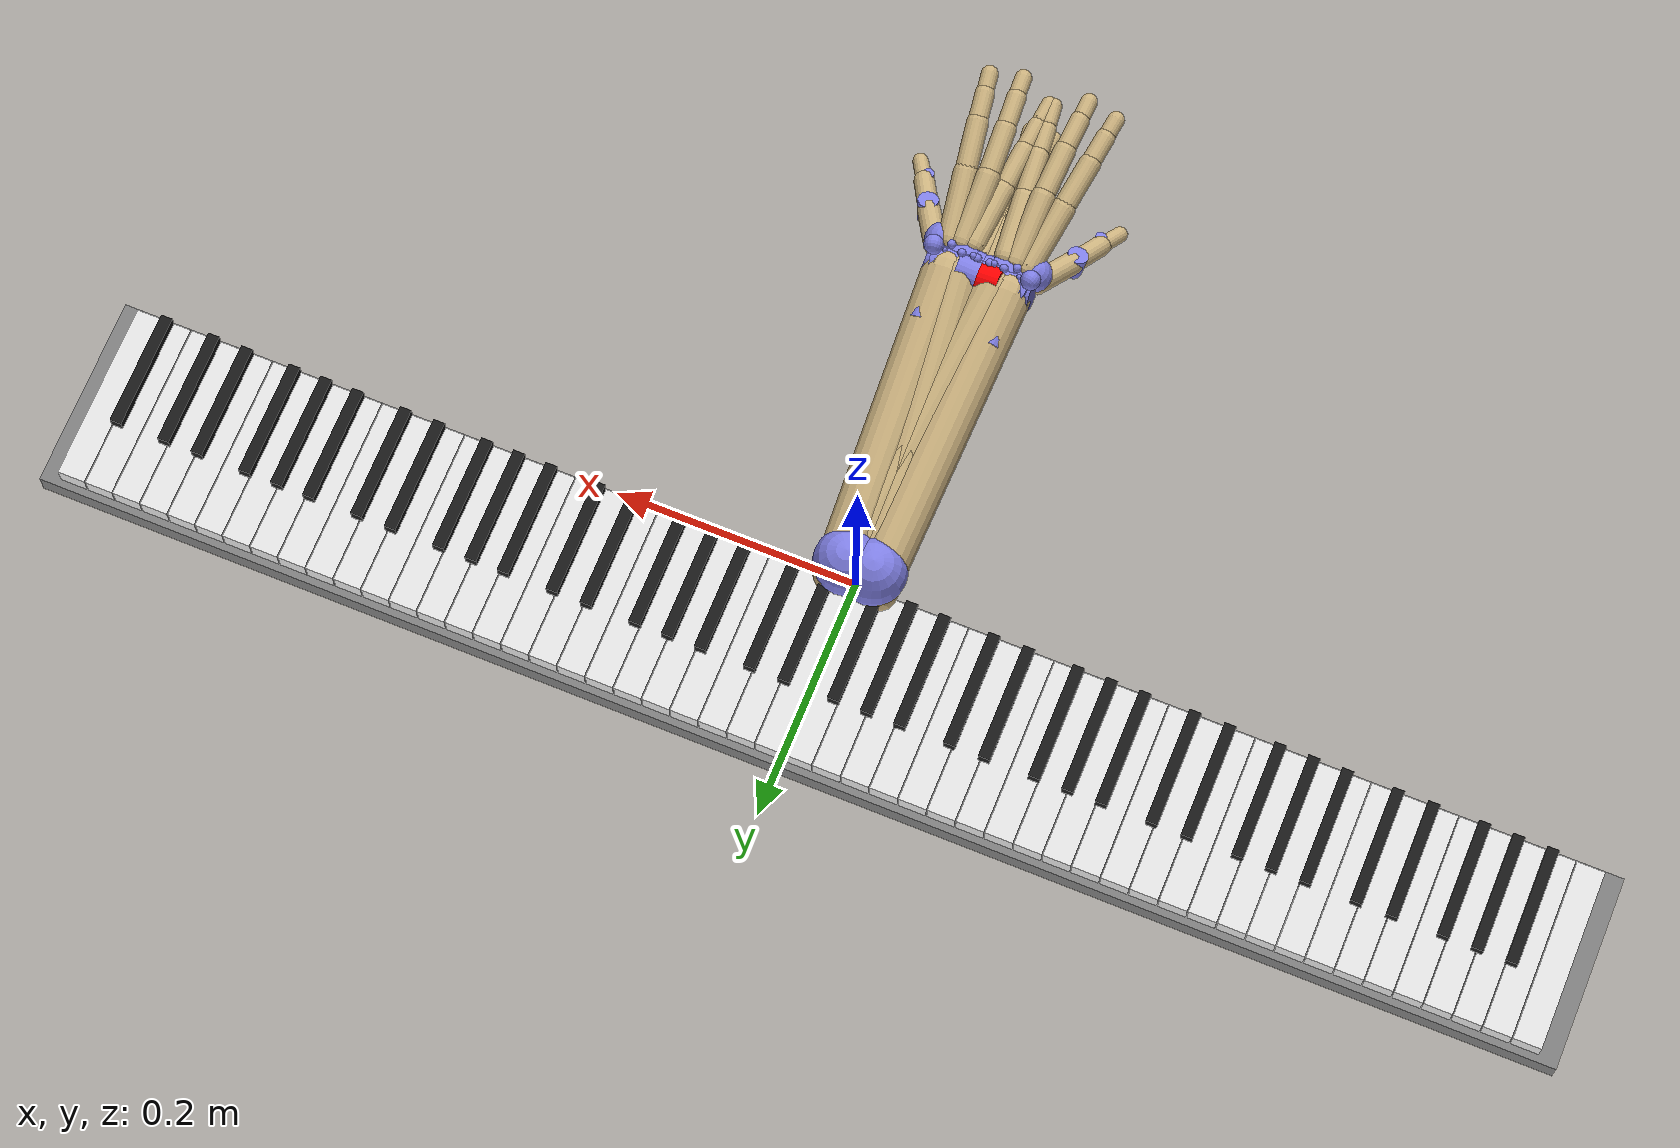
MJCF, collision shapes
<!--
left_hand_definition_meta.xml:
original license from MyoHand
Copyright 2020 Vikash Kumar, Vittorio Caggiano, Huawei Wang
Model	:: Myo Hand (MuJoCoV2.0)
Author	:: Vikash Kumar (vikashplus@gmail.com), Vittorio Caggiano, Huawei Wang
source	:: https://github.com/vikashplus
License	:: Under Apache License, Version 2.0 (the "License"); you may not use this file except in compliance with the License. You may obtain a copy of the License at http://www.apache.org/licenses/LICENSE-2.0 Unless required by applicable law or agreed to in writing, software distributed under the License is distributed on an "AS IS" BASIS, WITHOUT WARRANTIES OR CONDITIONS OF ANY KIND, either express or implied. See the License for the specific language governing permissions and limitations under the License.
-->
<mujoco model="MUSIC-Hand-v0.15">

    <include file="defaults.xml" />
    <include file="left_assets/left_hand_definition_meta.xml" />
    <include file="right_assets/right_hand_definition_meta.xml" />

    <include file="left_assets/left_hand_actuators_joint.xml"/>
    <include file="right_assets/right_hand_actuators_joint.xml"/>

    <asset>
    </asset>

    <visual>
        <global offwidth="1920" offheight="1080"/>
        <headlight ambient=".5 .5 .5" diffuse="0.50 0.50 0.50" specular="0.50 0.50 0.50"/>
        <rgba actuator='.7 .4 .4 1' actuatorpositive='1 0 0 1' actuatornegative='.175 .1 .1 1'/>
    </visual>

    <worldbody>

        <include file="left_assets/left_hand_6d_root.xml"/>
        <include file="right_assets/right_hand_6d_root.xml"/>

        <include file="piano_assets/piano_ds6.5.xml"/>

    </worldbody>

</mujoco>

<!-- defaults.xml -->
<mujocoinclude model="MUSIC-Hand-v0.15">
        <compiler inertiafromgeom="auto" angle="radian" balanceinertia="true" boundmass="0.001" boundinertia=".0001" meshdir="." texturedir="."/>
        <size njmax="1000" nconmax="400" nuser_jnt="1"/>
        <!-- 480 FPS -->
        <option timestep="0.00208333333" impratio="10" gravity="0 0 0"/>

        <asset>
            <texture name="texgeom" type="cube" builtin="flat" mark="cross" width="127" height="1278" rgb1="0.7 0.7 0.7" rgb2="0.9 0.9 0.9" markrgb="1 1 1" random="0.01"/>
            <material name="geom" texture="texgeom" texuniform="true"/>
            <material name="MatSkin" specular="0.2" shininess=".1" reflectance="0.5" rgba="0.9 .7 .5 1"/>
        </asset>

        <default>
            <default class="music-hand">
              <joint limited="true" damping="0.05" armature="1e-4" stiffness="0"/>
              <geom contype="0" conaffinity="0" condim="3" rgba="0.8 0.8 .8 1" solref=".02 1" solimp=".8 .8 .01" material="geom"/>
              <site size="0.0012" rgba=".2 .6 .2 1" group="3"/>
              <tendon width="0.001" rgba=".95 .3 .3 1" limited="false" />
              <default class="L:skin_arm">
                <geom type="capsule" group="5" contype="56" conaffinity="4" condim="1" rgba="0.8 0.7 .5 1" margin="0.001" material="MatSkin"/>
              </default>
              <default class="L:skin_palm">
                <geom type="capsule" group="4" contype="56" conaffinity="2" condim="3" rgba="0.8 0.7 .5 1" margin="0.001" material="MatSkin"/>
              </default>
              <default class="L:skin_finger">
                <geom type="capsule" group="5" contype="59" conaffinity="1" condim="3" rgba="0.8 0.7 .5 1" margin="0.001" material="MatSkin"/>
              </default>
              <default class="R:skin_arm">
                <geom type="capsule" group="5" contype="7" conaffinity="32" condim="1" rgba="0.8 0.7 .5 1" margin="0.001" material="MatSkin"/>
              </default>
              <default class="R:skin_palm">
                <geom type="capsule" group="4" contype="7" conaffinity="16" condim="3" rgba="0.8 0.7 .5 1" margin="0.001" material="MatSkin"/>
              </default>
              <default class="R:skin_finger">
                <geom type="capsule" group="5" contype="31" conaffinity="8" condim="3" rgba="0.8 0.7 .5 1" margin="0.001" material="MatSkin"/>
              </default>
              <default class="wrap">
                <geom rgba=".5 .5 .9 1" group="3" contype="0" conaffinity="0"/>
              </default>
              <default class="muscle">
                <muscle ctrllimited="true" ctrlrange="0 1" />
              </default>
            </default>
            <default class="white_key">
            <!--   range limit is decided by end position with travel depth of 0.01 i.e. arcsin(0.01/0.148)   -->
            <joint type="hinge" axis="1 0 0" pos="0 0 0" limited="true" range="-0.0676190854 0" solreflimit=".01 1" solimplimit=".95 .99 .001" stiffness="2" damping="0.05" armature="1e-3" />
            <geom group="2" type="box" condim="3" contype="9" conaffinity="0" solref=".02 1" solimp=".9 .95 .001" margin="0" priority="1" size="0.011313735 0.074 0.0105" pos="0 0.074 0" mass="0.04" rgba=".9 .9 .9 1"/>
            </default>
            <default class="black_key">
            <!--   range limit is decided by end position with travel depth of 0.008, i.e. arcsin(0.008/0.096)   -->
            <joint type="hinge" axis="1 0 0" pos="0 0 0" limited="true" range="-0.08333333333 0" solreflimit=".01 1" solimplimit=".95 .99 .001" stiffness="2" damping="0.05" armature="1e-3" />
            <!--   top width 0.0095, bottom width 0.011, bottom width with spacing 0.015   -->
            <geom group="2" type="box" condim="3" contype="9" conaffinity="0" solref=".02 1" solimp=".9 .95 .001" margin="0" priority="1" size="0.00475 0.048 0.01" pos="0 0.048 0" mass="0.02" rgba=".1 .1 .1 1"/>
            </default>
        </default>

      <custom>
        <numeric data="30" name="max_contact_points"/>
        <numeric data="500" name="max_geom_pairs"/>
      </custom>

</mujocoinclude>

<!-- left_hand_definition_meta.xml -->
<mujocoinclude model="MUSIC-Hand-v0.15">
        <asset>
            <!-- Modified from MyoHand. -->

            <mesh name="L:humerus" file="left_meshes/humerus.stl" scale="1 1 1"/>
            <mesh name="L:ulna" file="left_meshes/ulna.stl" scale="1 1 1"/>
            <mesh name="L:radius" file="left_meshes/radius.stl" scale="1 1 1"/>
            <mesh name="L:lunate" file="left_meshes/lunate.stl" scale="1 1 1"/>
            <mesh name="L:scaphoid" file="left_meshes/scaphoid.stl" scale="1 1 1"/>
            <mesh name="L:pisiform" file="left_meshes/pisiform.stl" scale="1 1 1"/>
            <mesh name="L:triquetrum" file="left_meshes/triquetrum.stl" scale="1 1 1"/>
            <mesh name="L:capitate" file="left_meshes/capitate.stl" scale="1 1 1"/>
            <mesh name="L:trapezium" file="left_meshes/trapezium.stl" scale="1 1 1"/>
            <mesh name="L:1mc" file="left_meshes/1mc.stl" scale="1 1 1"/>
            <mesh name="L:thumbprox" file="left_meshes/thumbprox.stl" scale="1 1 1"/>
            <mesh name="L:thumbdist" file="left_meshes/thumbdist.stl" scale="1 1 1"/>
            <mesh name="L:trapezoid" file="left_meshes/trapezoid.stl" scale="1 1 1"/>
            <mesh name="L:hamate" file="left_meshes/hamate.stl" scale="1 1 1"/>
            <mesh name="L:2mc" file="left_meshes/2mc.stl" scale="1 1 1"/>
            <mesh name="L:2proxph" file="left_meshes/2proxph.stl" scale="1 1 1"/>
            <mesh name="L:2midph" file="left_meshes/2midph.stl" scale="1 1 1"/>
            <mesh name="L:2distph" file="left_meshes/2distph.stl" scale="1 1 1"/>
            <mesh name="L:3mc" file="left_meshes/3mc.stl" scale="1 1 1"/>
            <mesh name="L:3proxph" file="left_meshes/3proxph.stl" scale="1 1 1"/>
            <mesh name="L:3midph" file="left_meshes/3midph.stl" scale="1 1 1"/>
            <mesh name="L:3distph" file="left_meshes/3distph.stl" scale="1 1 1"/>
            <mesh name="L:4mc" file="left_meshes/4mc.stl" scale="1 1 1"/>
            <mesh name="L:4proxph" file="left_meshes/4proxph.stl" scale="1 1 1"/>
            <mesh name="L:4midph" file="left_meshes/4midph.stl" scale="1 1 1"/>
            <mesh name="L:4distph" file="left_meshes/4distph.stl" scale="1 1 1"/>
            <mesh name="L:5mc" file="left_meshes/5mc.stl" scale="1 1 1"/>
            <mesh name="L:5proxph" file="left_meshes/5proxph.stl" scale="1 1 1"/>
            <mesh name="L:5midph" file="left_meshes/5midph.stl" scale="1 1 1"/>
            <mesh name="L:5distph" file="left_meshes/5distph.stl" scale="1 1 1"/>
        </asset>

        <contact>
            <exclude body1="L:proxph2" body2="L:proxph3"/>
            <exclude body1="L:proxph3" body2="L:proxph4"/>
            <exclude body1="L:proxph4" body2="L:proxph5"/>

            <exclude body1="L:proxph2" body2="L:proxph4"/>
            <exclude body1="L:proxph2" body2="L:proxph5"/>
            <exclude body1="L:proxph3" body2="L:proxph5"/>

        </contact>

</mujocoinclude>

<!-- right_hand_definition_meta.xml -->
<mujocoinclude model="MUSIC-Hand-v0.15">
        <asset>
            <!-- Extracted from MyoHand. -->

            <mesh name="R:humerus" file="right_meshes/humerus.stl" scale="1 1 1"/>
            <mesh name="R:ulna" file="right_meshes/ulna.stl" scale="1 1 1"/>
            <mesh name="R:radius" file="right_meshes/radius.stl" scale="1 1 1"/>
            <mesh name="R:lunate" file="right_meshes/lunate.stl" scale="1 1 1"/>
            <mesh name="R:scaphoid" file="right_meshes/scaphoid.stl" scale="1 1 1"/>
            <mesh name="R:pisiform" file="right_meshes/pisiform.stl" scale="1 1 1"/>
            <mesh name="R:triquetrum" file="right_meshes/triquetrum.stl" scale="1 1 1"/>
            <mesh name="R:capitate" file="right_meshes/capitate.stl" scale="1 1 1"/>
            <mesh name="R:trapezium" file="right_meshes/trapezium.stl" scale="1 1 1"/>
            <mesh name="R:1mc" file="right_meshes/1mc.stl" scale="1 1 1"/>
            <mesh name="R:thumbprox" file="right_meshes/thumbprox.stl" scale="1 1 1"/>
            <mesh name="R:thumbdist" file="right_meshes/thumbdist.stl" scale="1 1 1"/>
            <mesh name="R:trapezoid" file="right_meshes/trapezoid.stl" scale="1 1 1"/>
            <mesh name="R:hamate" file="right_meshes/hamate.stl" scale="1 1 1"/>
            <mesh name="R:2mc" file="right_meshes/2mc.stl" scale="1 1 1"/>
            <mesh name="R:2proxph" file="right_meshes/2proxph.stl" scale="1 1 1"/>
            <mesh name="R:2midph" file="right_meshes/2midph.stl" scale="1 1 1"/>
            <mesh name="R:2distph" file="right_meshes/2distph.stl" scale="1 1 1"/>
            <mesh name="R:3mc" file="right_meshes/3mc.stl" scale="1 1 1"/>
            <mesh name="R:3proxph" file="right_meshes/3proxph.stl" scale="1 1 1"/>
            <mesh name="R:3midph" file="right_meshes/3midph.stl" scale="1 1 1"/>
            <mesh name="R:3distph" file="right_meshes/3distph.stl" scale="1 1 1"/>
            <mesh name="R:4mc" file="right_meshes/4mc.stl" scale="1 1 1"/>
            <mesh name="R:4proxph" file="right_meshes/4proxph.stl" scale="1 1 1"/>
            <mesh name="R:4midph" file="right_meshes/4midph.stl" scale="1 1 1"/>
            <mesh name="R:4distph" file="right_meshes/4distph.stl" scale="1 1 1"/>
            <mesh name="R:5mc" file="right_meshes/5mc.stl" scale="1 1 1"/>
            <mesh name="R:5proxph" file="right_meshes/5proxph.stl" scale="1 1 1"/>
            <mesh name="R:5midph" file="right_meshes/5midph.stl" scale="1 1 1"/>
            <mesh name="R:5distph" file="right_meshes/5distph.stl" scale="1 1 1"/>
        </asset>

        <contact>
            <exclude body1="R:proxph2" body2="R:proxph3"/>
            <exclude body1="R:proxph3" body2="R:proxph4"/>
            <exclude body1="R:proxph4" body2="R:proxph5"/>

            <exclude body1="R:proxph2" body2="R:proxph4"/>
            <exclude body1="R:proxph2" body2="R:proxph5"/>
            <exclude body1="R:proxph3" body2="R:proxph5"/>

        </contact>
</mujocoinclude>

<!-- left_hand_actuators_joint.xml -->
<mujocoinclude model="MUSIC-Hand-v0.15">
        <actuator>
            <position name="L:elbow_x" joint="L:elbow_x" ctrllimited="true" ctrlrange="-2 2" forcelimited="true" forcerange="-50 50" kp="20" kv="2"/>
            <position name="L:elbow_y" joint="L:elbow_y" ctrllimited="true" ctrlrange="-2 2" forcelimited="true" forcerange="-50 50" kp="20" kv="2"/>
            <position name="L:elbow_z" joint="L:elbow_z" ctrllimited="true" ctrlrange="-2 2" forcelimited="true" forcerange="-50 50" kp="20" kv="2"/>
            <position name="L:elbow_rx" joint="L:elbow_rx" ctrllimited="true" ctrlrange="-2 2" forcelimited="true" forcerange="-50 50" kp="10" kv="1"/>
            <position name="L:elbow_ry" joint="L:elbow_ry" ctrllimited="true" ctrlrange="-2 2" forcelimited="true" forcerange="-50 50" kp="10" kv="1"/>
            <position name="L:elbow_rz" joint="L:elbow_rz" ctrllimited="true" ctrlrange="-2 2" forcelimited="true" forcerange="-50 50" kp="10" kv="1"/>

            <position name="L:pro_sup" joint="L:pro_sup" ctrllimited="true" ctrlrange="-2 2" forcelimited="true" forcerange="-20 20" kp="10" kv="0.1" />
            <position name="L:deviation" joint="L:deviation" ctrllimited="true" ctrlrange="-2 2" forcelimited="true" forcerange="-20 20" kp="10" kv="0.1" />
            <position name="L:flexion" joint="L:flexion" ctrllimited="true" ctrlrange="-2 2" forcelimited="true" forcerange="-20 20" kp="10" kv="0.1" />

            <position name="L:cmc_abduction" joint="L:cmc_abduction" ctrllimited="true" ctrlrange="-2 2" forcelimited="true" forcerange="-10 10" kp="10" kv="0.1" />
            <position name="L:cmc_flexion" joint="L:cmc_flexion" ctrllimited="true" ctrlrange="-2 2" forcelimited="true" forcerange="-10 10" kp="10" kv="0.1" />
            <position name="L:mp_flexion" joint="L:mp_flexion" ctrllimited="true" ctrlrange="-2 2" forcelimited="true" forcerange="-10 10" kp="10" kv="0.1" />
            <position name="L:ip_flexion" joint="L:ip_flexion" ctrllimited="true" ctrlrange="-2 2" forcelimited="true" forcerange="-10 10" kp="10" kv="0.1" />
            <position name="L:mcp2_flexion" joint="L:mcp2_flexion" ctrllimited="true" ctrlrange="-2 2" forcelimited="true" forcerange="-10 10" kp="10" kv="0.1" />
            <position name="L:mcp2_abduction" joint="L:mcp2_abduction" ctrllimited="true" ctrlrange="-2 2" forcelimited="true" forcerange="-10 10" kp="10" kv="0.1" />
            <position name="L:pm2_flexion" joint="L:pm2_flexion" ctrllimited="true" ctrlrange="-2 2" forcelimited="true" forcerange="-10 10" kp="10" kv="0.1" />
            <position name="L:md2_flexion" joint="L:md2_flexion" ctrllimited="true" ctrlrange="-2 2" forcelimited="true" forcerange="-10 10" kp="10" kv="0.1" />
            <position name="L:mcp3_flexion" joint="L:mcp3_flexion" ctrllimited="true" ctrlrange="-2 2" forcelimited="true" forcerange="-10 10" kp="10" kv="0.1" />
            <position name="L:mcp3_abduction" joint="L:mcp3_abduction" ctrllimited="true" ctrlrange="-2 2" forcelimited="true" forcerange="-10 10" kp="10" kv="0.1" />
            <position name="L:pm3_flexion" joint="L:pm3_flexion" ctrllimited="true" ctrlrange="-2 2" forcelimited="true" forcerange="-10 10" kp="10" kv="0.1" />
            <position name="L:md3_flexion" joint="L:md3_flexion" ctrllimited="true" ctrlrange="-2 2" forcelimited="true" forcerange="-10 10" kp="10" kv="0.1" />
            <position name="L:mcp4_flexion" joint="L:mcp4_flexion" ctrllimited="true" ctrlrange="-2 2" forcelimited="true" forcerange="-10 10" kp="10" kv="0.1" />
            <position name="L:mcp4_abduction" joint="L:mcp4_abduction" ctrllimited="true" ctrlrange="-2 2" forcelimited="true" forcerange="-10 10" kp="10" kv="0.1" />
            <position name="L:pm4_flexion" joint="L:pm4_flexion" ctrllimited="true" ctrlrange="-2 2" forcelimited="true" forcerange="-10 10" kp="10" kv="0.1" />
            <position name="L:md4_flexion" joint="L:md4_flexion" ctrllimited="true" ctrlrange="-2 2" forcelimited="true" forcerange="-10 10" kp="10" kv="0.1" />
            <position name="L:mcp5_flexion" joint="L:mcp5_flexion" ctrllimited="true" ctrlrange="-2 2" forcelimited="true" forcerange="-10 10" kp="10" kv="0.1" />
            <position name="L:mcp5_abduction" joint="L:mcp5_abduction" ctrllimited="true" ctrlrange="-2 2" forcelimited="true" forcerange="-10 10" kp="10" kv="0.1" />
            <position name="L:pm5_flexion" joint="L:pm5_flexion" ctrllimited="true" ctrlrange="-2 2" forcelimited="true" forcerange="-10 10" kp="10" kv="0.1" />
            <position name="L:md5_flexion" joint="L:md5_flexion" ctrllimited="true" ctrlrange="-2 2" forcelimited="true" forcerange="-10 10" kp="10" kv="0.1" />
        </actuator>
</mujocoinclude>

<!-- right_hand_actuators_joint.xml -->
<mujocoinclude model="MUSIC-Hand-v0.15">
        <actuator>
            <position name="R:elbow_x" joint="R:elbow_x" ctrllimited="true" ctrlrange="-2 2" forcelimited="true" forcerange="-50 50" kp="20" kv="2"/>
            <position name="R:elbow_y" joint="R:elbow_y" ctrllimited="true" ctrlrange="-2 2" forcelimited="true" forcerange="-50 50" kp="20" kv="2"/>
            <position name="R:elbow_z" joint="R:elbow_z" ctrllimited="true" ctrlrange="-2 2" forcelimited="true" forcerange="-50 50" kp="20" kv="2"/>
            <position name="R:elbow_rx" joint="R:elbow_rx" ctrllimited="true" ctrlrange="-2 2" forcelimited="true" forcerange="-50 50" kp="10" kv="1"/>
            <position name="R:elbow_ry" joint="R:elbow_ry" ctrllimited="true" ctrlrange="-2 2" forcelimited="true" forcerange="-50 50" kp="10" kv="1"/>
            <position name="R:elbow_rz" joint="R:elbow_rz" ctrllimited="true" ctrlrange="-2 2" forcelimited="true" forcerange="-50 50" kp="10" kv="1"/>

            <position name="R:pro_sup" joint="R:pro_sup" ctrllimited="true" ctrlrange="-2 2" forcelimited="true" forcerange="-20 20" kp="10" kv="0.1" />
            <position name="R:deviation" joint="R:deviation" ctrllimited="true" ctrlrange="-2 2" forcelimited="true" forcerange="-20 20" kp="10" kv="0.1" />
            <position name="R:flexion" joint="R:flexion" ctrllimited="true" ctrlrange="-2 2" forcelimited="true" forcerange="-20 20" kp="10" kv="0.1" />

            <position name="R:cmc_abduction" joint="R:cmc_abduction" ctrllimited="true" ctrlrange="-2 2" forcelimited="true" forcerange="-10 10" kp="10" kv="0.1" />
            <position name="R:cmc_flexion" joint="R:cmc_flexion" ctrllimited="true" ctrlrange="-2 2" forcelimited="true" forcerange="-10 10" kp="10" kv="0.1" />
            <position name="R:mp_flexion" joint="R:mp_flexion" ctrllimited="true" ctrlrange="-2 2" forcelimited="true" forcerange="-10 10" kp="10" kv="0.1" />
            <position name="R:ip_flexion" joint="R:ip_flexion" ctrllimited="true" ctrlrange="-2 2" forcelimited="true" forcerange="-10 10" kp="10" kv="0.1" />
            <position name="R:mcp2_flexion" joint="R:mcp2_flexion" ctrllimited="true" ctrlrange="-2 2" forcelimited="true" forcerange="-10 10" kp="10" kv="0.1" />
            <position name="R:mcp2_abduction" joint="R:mcp2_abduction" ctrllimited="true" ctrlrange="-2 2" forcelimited="true" forcerange="-10 10" kp="10" kv="0.1" />
            <position name="R:pm2_flexion" joint="R:pm2_flexion" ctrllimited="true" ctrlrange="-2 2" forcelimited="true" forcerange="-10 10" kp="10" kv="0.1" />
            <position name="R:md2_flexion" joint="R:md2_flexion" ctrllimited="true" ctrlrange="-2 2" forcelimited="true" forcerange="-10 10" kp="10" kv="0.1" />
            <position name="R:mcp3_flexion" joint="R:mcp3_flexion" ctrllimited="true" ctrlrange="-2 2" forcelimited="true" forcerange="-10 10" kp="10" kv="0.1" />
            <position name="R:mcp3_abduction" joint="R:mcp3_abduction" ctrllimited="true" ctrlrange="-2 2" forcelimited="true" forcerange="-10 10" kp="10" kv="0.1" />
            <position name="R:pm3_flexion" joint="R:pm3_flexion" ctrllimited="true" ctrlrange="-2 2" forcelimited="true" forcerange="-10 10" kp="10" kv="0.1" />
            <position name="R:md3_flexion" joint="R:md3_flexion" ctrllimited="true" ctrlrange="-2 2" forcelimited="true" forcerange="-10 10" kp="10" kv="0.1" />
            <position name="R:mcp4_flexion" joint="R:mcp4_flexion" ctrllimited="true" ctrlrange="-2 2" forcelimited="true" forcerange="-10 10" kp="10" kv="0.1" />
            <position name="R:mcp4_abduction" joint="R:mcp4_abduction" ctrllimited="true" ctrlrange="-2 2" forcelimited="true" forcerange="-10 10" kp="10" kv="0.1" />
            <position name="R:pm4_flexion" joint="R:pm4_flexion" ctrllimited="true" ctrlrange="-2 2" forcelimited="true" forcerange="-10 10" kp="10" kv="0.1" />
            <position name="R:md4_flexion" joint="R:md4_flexion" ctrllimited="true" ctrlrange="-2 2" forcelimited="true" forcerange="-10 10" kp="10" kv="0.1" />
            <position name="R:mcp5_flexion" joint="R:mcp5_flexion" ctrllimited="true" ctrlrange="-2 2" forcelimited="true" forcerange="-10 10" kp="10" kv="0.1" />
            <position name="R:mcp5_abduction" joint="R:mcp5_abduction" ctrllimited="true" ctrlrange="-2 2" forcelimited="true" forcerange="-10 10" kp="10" kv="0.1" />
            <position name="R:pm5_flexion" joint="R:pm5_flexion" ctrllimited="true" ctrlrange="-2 2" forcelimited="true" forcerange="-10 10" kp="10" kv="0.1" />
            <position name="R:md5_flexion" joint="R:md5_flexion" ctrllimited="true" ctrlrange="-2 2" forcelimited="true" forcerange="-10 10" kp="10" kv="0.1" />
        </actuator>
</mujocoinclude>

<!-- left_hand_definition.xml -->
<mujocoinclude model="MUSIC-Hand-v0.15">
<!-- Modified from MyoHand and add five additional muscle-tendon units: AdP, FPB, APB, ADM, and FDM. -->

                <geom name="L:Elbow_PT_ECRL_wrap" type="sphere" size="0.027" pos="0.0111 -0.0096  0.0173" class="wrap"/>
                <geom name="L:Elbow_PT_FCU_wrap" type="sphere" size="0.015" pos="0.0111  0.0004 -0.0207" class="wrap"/>
                <site name="L:Elbow_PT_ECRL_site_ECRL_side" pos="-0.0239 0.0032 0.0523"/>
                <site name="L:Elbow_PT_FCU_site_FCU_side" pos="-0.0239  0.0032 -0.0277"/>
                <site name="L:ECRL-P1" pos="0.0134  0.0295  0.0214"/>
                <site name="L:ECRB-P1" pos="-0.0074 -0.0001 0.0293"/>
                <site name="L:ECU-P1" pos="0.0053  0.0009  0.0311"/>
                <site name="L:FCR-P1" pos="-0.0015  0.0123 -0.0247"/>
                <site name="L:FCU-P1" pos="0.0039  0.013  -0.0265"/>
                <site name="L:PL-P1" pos="0.0015  0.0152 -0.0263"/>
                <site name="L:PT-P1" pos="0.0025  0.0145 -0.0242"/>
                <site name="L:FDS5-P1" pos="0.0019  0.0144 -0.0263"/>
                <site name="L:FDS4-P1" pos="0.0013  0.0116 -0.025"/>
                <site name="L:EDC5-P1" pos="0.0065  0.0021  0.031"/>
                <site name="L:EDC4-P1" pos="0.0077  0.001   0.0301"/>
                <site name="L:EDC3-P1" pos="0.0056  0.0006  0.0318"/>
                <site name="L:EDC2-P1" pos="0.0055  0.0014  0.031"/>
                <site name="L:EDM-P1" pos="0.0052  0.0012  0.0308"/>

                <geom class="L:skin_arm" size="0.015" fromto=".02 0 .005 -.005 -0.2 0.04"/>
                <geom mesh="L:ulna" name="L:ulna" type="mesh"/>
                <inertial pos="-0.00971783 -0.0959509 0.024286" mass="1.1053" fullinertia="0.00541309 0.00115318 0.00494361 0.00031686 -7.615e-05 0.00109169"/>
                <geom name="L:PQ2_wrap" pos="0.0012 -0.2092 0.0428" quat="0.540178 0.481989 0.422693 -0.545183" class="wrap" size="0.007 0.005" type="cylinder"/>
                <site name="L:ECU-P2" pos="0.0139 -0.032 0.0295"/>
                <site name="L:ECU-P3" pos="0.017 -0.0543 0.0287"/>
                <site name="L:ECU-P4" pos="0.0179 -0.0957 0.0328"/>
                <site name="L:PT-P2" pos="-0.0085 -0.0337 -0.0143"/>
                <site name="L:PT-P3" pos="-0.0122 -0.0652 -0.0022"/>
                <site name="L:PQ-P2" pos="-0.0019 -0.2097 0.0363"/>
                <site name="L:FDS3-P1" pos="0.0067 -0.0271 -0.0019"/>
                <site name="L:FDS2-P1" pos="0.0068 -0.0282 -0.0014"/>
                <site name="L:FDP5-P1" pos="0.0063 -0.0321 0.0025"/>
                <site name="L:FDP4-P1" pos="0.005 -0.0337 0.0027"/>
                <site name="L:FDP3-P1" pos="0.0052 -0.0333 0.0021"/>
                <site name="L:FDP2-P1" pos="0.0065 -0.0318 0.0028"/>
                <site name="L:EDM-P2" pos="0.0098 -0.0391 0.0308"/>
                <site name="L:EDM-P3" pos="0.0076 -0.0827 0.0365"/>
                <site name="L:EIP-P1" pos="0.0039 -0.1665 0.0368"/>
                <site name="L:EIP-P2" pos="-0.0017 -0.1747 0.0405"/>
                <site name="L:EPL-P1" pos="0.0141 -0.0971 0.0295"/>
                <site name="L:PQ2_site_PQ_side" pos="0.0012 -0.2092 0.0428"/>
                <body name="L:radius" pos="-0.0004 -0.011503 0.019999">
                    <joint axis="-0.017161 -0.992666 0.119668" name="L:pro_sup" pos="-0 0 0" range="-1.5708 1.5708" damping="0.5"/>
                    <geom class="L:skin_arm" size="0.02" fromto="-0.015 0 -.005 -0.025 -0.24 0.025"/>
                    <geom class="L:skin_arm" size="0.02" fromto=".01 0 -.010 -0.015 -0.24 0.025"/>
                    <geom mesh="L:radius" name="L:radius" type="mesh"/>
                    <inertial pos="-0.0336341 -0.181559 0.0156" mass="0.23359" fullinertia="0.00043855 8.859e-05 0.00040258 3.014e-05 -4.24e-06 6.418e-05"/>
                    <geom name="L:SUP_wrap" pos="-0.0045 -0.0437 0.0059" quat="0.348354 0.118086 -0.653837 0.661213" class="wrap" size="0.008 0.02" type="cylinder"/>
                    <geom name="L:PQ1_wrap" pos="-0.0281 -0.1986 0.0288" quat="0.15975 -0.156797 0.702725 0.675331" class="wrap" size="0.01 0.005" type="cylinder"/>
                    <geom name="L:ECU_torus_wrap" pos="0.0163 -0.2417 0.0349" quat="0.868975 -0.476593 0.0126204 -0.132601" class="wrap" size="0.003"/>
                    <site name="L:ECRL-P2" pos="-0.032 -0.1346 0.0278"/>
                    <site name="L:ECRL-P3" pos="-0.0424 -0.2368 0.0362"/>
                    <site name="L:ECRB-P2" pos="-0.029 -0.1309 0.0238"/>
                    <site name="L:ECRB-P3" pos="-0.0355 -0.228 0.0394"/>
                    <site name="L:ECU-P5" pos="0.0142 -0.227 0.0348"/>
                    <site name="L:FCR-P2" pos="-0.0211 -0.2194 0.0013"/>
                    <site name="L:FCU-P3" pos="-0.0108 -0.2233 0.0097"/>
                    <site name="L:FCU-P2" pos="-0.0095 -0.1841 0.0005"></site>
                    <site name="L:PL-P2" pos="-0.0253 -0.2392 -0.0028"/>
                    <site name="L:PT-P5" pos="-0.0254 -0.1088 0.0198"/>
                    <site name="L:PT-P4" pos="-0.0236 -0.0934 0.0094"/>
                    <site name="L:PQ-P1" pos="-0.0324 -0.2 0.0196"/>
                    <site name="L:FDS5-P2" pos="-0.0138 -0.1872 0.002"/>
                    <site name="L:FDS4-P2" pos="-0.0157 -0.1867 0.0027"/>
                    <site name="L:FDS3-P2" pos="-0.019 -0.1871 0.0042"/>
                    <site name="L:FDS2-P2" pos="-0.0214 -0.1862 0.0055"/>
                    <site name="L:FDP5-P2" pos="-0.0141 -0.1852 0.0086"/>
                    <site name="L:FDP4-P2" pos="-0.0158 -0.1863 0.008"/>
                    <site name="L:FDP3-P2" pos="-0.0191 -0.1864 0.0078"/>
                    <site name="L:FDP2-P2" pos="-0.0208 -0.1856 0.0092"/>
                    <site name="L:EDC5-P3" pos="-0.0099 -0.223 0.0362"/>
                    <site name="L:EDC5-P2" pos="-0.0013 -0.0383 0.013"/>
                    <site name="L:EDC4-P3" pos="-0.0088 -0.2237 0.0428"/>
                    <site name="L:EDC4-P2" pos="-0.0026 -0.0393 0.0144"/>
                    <site name="L:EDC3-P3" pos="-0.0144 -0.2232 0.0422"/>
                    <site name="L:EDC3-P2" pos="-0.0032 -0.0389 0.0142"/>
                    <site name="L:EDC2-P3" pos="-0.0153 -0.2231 0.042"/>
                    <site name="L:EDC2-P2" pos="-0.0023 -0.0386 0.0137"/>
                    <site name="L:EDM-P4" pos="-0.0045 -0.2264 0.0368"/>
                    <site name="L:EIP-P3" pos="-0.0108 -0.2278 0.0366"/>
                    <site name="L:EPL-P2" pos="-0.0012 -0.1367 0.0227"/>
                    <site name="L:EPL-P3" pos="-0.027 -0.2187 0.0383"/>
                    <site name="L:EPL-P4" pos="-0.0338 -0.2275 0.0461"/>
                    <site name="L:EPL-P5" pos="-0.0423 -0.2377 0.0417"/>
                    <site name="L:EPB-P1" pos="-0.0192 -0.147 0.0211"/>
                    <site name="L:EPB-P2" pos="-0.0228 -0.1586 0.0266"/>
                    <site name="L:EPB-P3" pos="-0.0383 -0.1972 0.0383"/>
                    <site name="L:EPB-P4" pos="-0.0524 -0.2361 0.027"/>
                    <site name="L:FPL-P1" pos="-0.0097 -0.0946 0.0177"/>
                    <site name="L:FPL-P2" pos="-0.0166 -0.1352 0.0192"/>
                    <site name="L:FPL-P3" pos="-0.0187 -0.1793 0.0199"/>
                    <site name="L:FPL-P4" pos="-0.038 -0.2317 0.0158"/>
                    <site name="L:APL-P1" pos="-0.0115 -0.0948 0.0168"/>
                    <site name="L:APL-P2" pos="-0.0303 -0.1397 0.0351"/>
                    <site name="L:APL-P3" pos="-0.0399 -0.1607 0.034"/>
                    <site name="L:APL-P4" pos="-0.044 -0.1784 0.0313"/>
                    <site name="L:APL-P5" pos="-0.055 -0.2308 0.0237"/>
                    <site name="L:ECU_torus_site_ECU_side" pos="0.0163 -0.2417 0.0349"/>
                    <body name="L:lunate" pos="-0.018 -0.242 0.025">
                        <joint axis="0 -0 -1" name="L:deviation" pos="-0 0 0" range="-0.174533 0.436332" damping="0.25"/>
                        <joint axis="1 -0 -0" name="L:flexion" pos="-0 0 0" range="-0.785398 0.785398" damping="0.25"/>
                        <geom mesh="L:lunate" name="L:lunate" type="mesh"/>
                        <geom name="L:WristExtensor_wrap" pos="-0.0007 0 0.003" quat="0.807649 -0.0333177 -0.588355 -0.0207694" class="wrap" size="0.008 0.02" type="cylinder"/>
                        <geom name="L:WristFlexor_wrap" pos="-0 -0.01 -0.004" quat="0.807649 -0.0333177 -0.588355 -0.0207694" class="wrap" size="0.007 0.02" type="cylinder"/>
                        <geom name="L:ExtensorEllipse_ellipsoid_wrap" pos="0.00145969 -0.0120017 -0.00892632" quat="0.977473 -0.106567 -0.15459 -0.0963907" class="wrap" size="0.0237409"/>
                        <geom name="L:FDS_ellipsoid_wrap" type="cylinder" size="0.013 0.025" pos="-0.0012 -0.0057 -0.0003" euler="0.00837758 -1.48 0.0171042" class="wrap"/>
                        <geom name="L:FDP_ellipsoid_wrap" type="cylinder" size="0.013 0.025" pos="0.0022 -0.0069 0.0032" euler="-1.46747 -1.37 -0.121824" class="wrap"/>
                        <geom name="L:EDM_ellipsoid_wrap" type="cylinder" size="0.014 0.018" pos="0.0167 -0.0022 0.0048" euler="2.9627 -1.73 -0.117984" class="wrap" rgba="1 0 0 1"/>
                        <geom name="L:FPL_ellipsoid_wrap" type="sphere" size="0.015" pos="-0.02 -0.025 -0.0033" class="wrap"/>
                        <geom name="L:ECRL_torus_wrap" pos="-0.0222 -0.0096 0.0208" quat="0.637339 0.675155 0.168467 -0.331034" class="wrap" size="0.008"/>
                        <geom name="L:ECRB_torus_wrap" pos="-0.0126 -0.0095 0.0186" quat="0.78744 0.610837 0.011177 0.0818018" class="wrap" size="0.002"/>
                        <geom name="L:FCR_torus_wrap" pos="-0.0032 -0.0045 -0.019" quat="0.71204 -0.696183 0.0894345 -0.0181554" class="wrap" size="0.0015"/>

                        <geom name="L:EDCL_torus_wrap" pos="0.0128 -0.0133 0.0148" quat="0.386237 0.907673 -0.159784 -0.037683" class="wrap" size="0.004"/>
                        <geom name="L:EDCR_torus_wrap" pos="0.0098 -0.0137 0.0166" quat="0.516906 0.814718 0.18962 -0.1819" class="wrap" size="0.003"/>
                        <geom name="L:EDCM_torus_wrap" pos="0.0007 -0.0117 0.0191" quat="0.516192 0.831214 0.100219 -0.180516" class="wrap" size="0.0035"/>
                        <geom name="L:EDCI_torus_wrap" pos="-0.009 -0.0149 0.0211" quat="0.660055 0.749868 -0.0267535 -0.0361877" class="wrap" size="0.0035"/>
                        <site name="L:ExtensorEllipse_ellipsoid_site_EIP_side" pos="0.0195105 -0.00430577 0.0636576"/>

                        <site name="L:FDS_ellipsoid_site_FDS5_side" pos="0.00481002 -0.034454 -0.0213554"/>
                        <site name="L:FDS_ellipsoid_site_FDS4_side" pos="0.00481002 -0.034454 -0.0213554" />
                        <site name="L:FDS_ellipsoid_site_FDS3_side" pos="0.00481002 -0.034454 -0.0213554" />
                        <site name="L:FDS_ellipsoid_site_FDS2_side" pos="0.00481002 -0.034454 -0.0213554" />

                        <site name="L:FDP_ellipsoid_site_FDP5_side" pos="0.00481002 -0.034454 -0.0213554"/>
                        <site name="L:FDP_ellipsoid_site_FDP4_side" pos="0.00481002 -0.034454 -0.0213554"/>
                        <site name="L:FDP_ellipsoid_site_FDP3_side" pos="0.00481002 -0.034454 -0.0213554"/>
                        <site name="L:FDP_ellipsoid_site_FDP2_side" pos="0.00481002 -0.034454 -0.0213554"/>
                        <site name="L:EDM_ellipsoid_site_EDM_side" pos="0.0167 0.0022 0.015"/>

                        <site name="L:ECRL_torus_site_ECRL_side" pos="-0.0222 -0.0096 0.0208"/>
                        <site name="L:ECRB_torus_site_ECRB_side" pos="-0.0126 -0.0095 0.0186"/>
                        <site name="L:FCR_torus_site_FCR_side" pos="-0.0032 -0.0045 -0.019"/>

                        <site name="L:EDCL_torus_site_EDC5_side" pos="0.0128 -0.0133 0.0148"/>
                        <site name="L:EDCR_torus_site_EDC4_side" pos="0.0098 -0.0137 0.0166"/>
                        <site name="L:EDCM_torus_site_EDC3_side" pos="0.0007 -0.0117 0.0191"/>
                        <site name="L:EDCI_torus_site_EDC2_side" pos="-0.009 -0.0149 0.0211"/>
                        <body name="L:scaphoid" pos="-0.012345 -0.004464 -0.001254">
                            <geom mesh="L:scaphoid" name="L:scaphoid" type="mesh"/>
                            <inertial pos="-0 0 0" mass="0.02" fullinertia="0.0001 0.0001 0.0001 0 0 0"/>
                        </body>
                        <body name="L:pisiform" pos="0.013388 -0.009886 -0.010593">
                            <geom mesh="L:pisiform" name="L:pisiform" type="mesh"/>
                            <geom name="L:FCU_wrap" pos="-0 0 0.006" quat="0.600794 -0.4144 -0.573042 0.372748" class="wrap" size="0.005 0.01" type="cylinder"/>
                            <inertial pos="-0 0 0" mass="0.02" fullinertia="0.0001 0.0001 0.0001 0 0 0"/>
                            <site name="L:FCU-P4" pos="-0.001 0.003 -0.01"/>
                            <!-- MUSIC-Hand Added Insertion-->
                            <site name="L:ADM-P2" pos="0.002 0.000 -0.002"></site>
                            <!-- MUSIC-Hand Added Insertion End-->
                        </body>
                        <body name="L:triquetrum" pos="0.010784 -0.007499 -0.001289">
                            <geom mesh="L:triquetrum" name="L:triquetrum" type="mesh"/>
                            <inertial pos="-0 0 0" mass="0.02" fullinertia="0.0001 0.0001 0.0001 0 0 0"/>
                        </body>
                        <body name="L:capitate" pos="-0.003992 -0.015054 0.002327">
                            <geom mesh="L:capitate" name="L:capitate" type="mesh"/>
                            <site name="L:PL-P3" pos="-0.0092 -0.019 -0.0175"/>
                            <site name="L:FDS5-P3" pos="0.0024 -0.0139 -0.0138"/>
                            <site name="L:FDS4-P3" pos="0.0008 -0.0134 -0.0136"/>
                            <site name="L:FDS3-P3" pos="-0.0068 -0.0138 -0.014"/>
                            <site name="L:FDS2-P3" pos="-0.0089 -0.0137 -0.0139"/>
                            <site name="L:FDP5-P3" pos="0.0009 -0.0103 -0.0119"/>
                            <site name="L:FDP4-P3" pos="-0.0011 -0.0118 -0.0118"/>
                            <site name="L:FDP3-P3" pos="-0.0034 -0.0128 -0.0114"/>
                            <site name="L:FDP2-P3" pos="-0.009 -0.0117 -0.0121"/>
                            <site name="L:EPL-P6" pos="-0.0243 0.0001 0.0061"/>
                            <site name="L:EPB-P5" pos="-0.0312 0.0026 -0.0033"/>
                            <site name="L:FPL-P5" pos="-0.0187 0.0088 -0.0155"></site>
                            <body name="L:trapezium" pos="-0.015293 -0.004569 -0.010308">
                                <geom mesh="L:trapezium" name="L:trapezium" type="mesh"/>
                                <inertial pos="-0 0 0" mass="0.02" fullinertia="0.0001 0.0001 0.0001 0 0 0"/>
                                <geom name="L:Trpzm_wrap" pos="-0.002 -0.003 0" quat="0.708942 0.660448 -0.181023 -0.16864" class="wrap" size="0.011"/>
                                <site name="L:EPL-P7" pos="-0.0081 -0.0046 0.0099"/>
                                <site name="L:OP-P1" pos="0.011 -0.005 -0.004"/>
                                <!-- MUSIC-Hand Added Insertion-->
                                <site name="L:FPB-P1" pos="-0.000 0.000 -0.006"/>
                                <site name="L:APB-P1" pos="-0.000 0.000 -0.006"/>
                                <!-- MUSIC-Hand Added Insertion End-->

                                <!-- ======= target site 1 ======= -->

                                <!-- ======= target site 2 ======= -->

                                <!-- THUMB FINGER -->
                                <body name="L:firstmc" pos="-0.0072 -0.0054 -0.0025">
                                    <joint axis="-0.042399 0.665286 -0.745384" name="L:cmc_abduction" pos="-0 0 0" range="-0.5 0.78"/>
                                    <joint axis="0.495557 -0.731736 -0.467959" name="L:cmc_flexion" pos="-0 0 0" range="-0.78 0.7"/>
                                    <geom name="L:1mcskin" class="L:skin_finger" size="0.0095" fromto=".002 0.004 0.003 -0.0165 -0.0292 -0.0127"/>
                                    <geom mesh="L:1mc" name="L:1mc" type="mesh"/>
                                    <geom name="L:MPthumb_wrap" type="cylinder" size="0.0085 0.01" pos="-0.0177 -0.0305 -0.0143" euler="0.32131512 -0.11013028 0.83479098" class="wrap"/>
                                    <inertial pos="-0.0078 -0.0147 -0.006" mass="0.016" fullinertia="1.2e-06 7.1e-07 1.3e-06 4.7e-07 2.5e-07 -4.1e-07"/>
                                    <site name="L:EPL-P8" pos="-0.0066 -0.0043 0.0079"/>
                                    <site name="L:EPL-P9" pos="-0.0216 -0.0242 -0.0053"/>
                                    <site name="L:EPB-P6" pos="-0.0144 -0.0034 -0.004"/>
                                    <site name="L:EPB-P7" pos="-0.0217 -0.023 -0.0114"/>
                                    <!-- MUSIC-Hand Added Insertion-->
                                    <site name="L:APB-P2" pos="-0.015 -0.022 -0.020"/>
                                    <!-- MUSIC-Hand Added Insertion End-->
                                    <site name="L:FPL-P7" pos="0.0061 -0.0162 -0.0094"></site>
                                    <site name="L:FPL-P8" pos="-0.0021 -0.023 -0.0096"></site>
                                    <site name="L:APL-P6" pos="-0 0.006 -0.01"></site>
                                    <site name="L:APL-P7" pos="-0.0063 0.0032 -0.0059"></site>
                                    <site name="L:APL-P8" pos="-0.0083 -0.0059 -0.006"></site>
                                    <site name="L:OP-P2" pos="-0.011 -0.03 -0.016"/>
                                    <site name="L:MPthumb_site_EPB_side" pos="-0.0252901 -0.0179637 -0.00935966" />
                                    <site name="L:MPthumb_site_FPL_side" pos="-0.0177 -0.0305 -0.0143"/>
                                    <body name="L:proximal_thumb" pos="-0.0165 -0.0292 -0.0127">
                                        <joint axis="-0.084295 0.203488 -0.975442" name="L:mp_flexion" pos="-0 0 0" range="-0.785398 0.698132"/>
                                        <geom class="L:skin_finger" size="0.0085" fromto="-0 0 0 -0.014 -0.0259 -0.0101"/>
                                        <geom mesh="L:thumbprox" name="L:thumbprox" type="mesh"/>
                                        <geom name="L:IPthumb_wrap" type="cylinder" size="0.00450000 0.005" pos="-0.0121 -0.0302 -0.0096" euler="0.30473449 -0.01291544 -0.08796459" class="wrap"/>
                                        <inertial pos="-0.0096 -0.0163 -0.0063" mass="0.0079" fullinertia="2.6e-07 7.1e-07 2.9e-07 1e-07 4e-08 -6e-08"/>
                                        <site name="L:EPL-P10" pos="-0.0115 -0.0036 0.0016"/>
                                        <site name="L:EPL-P11" pos="-0.0192 -0.0265 -0.0104"/>
                                        <site name="L:EPB-P8" pos="-0.0093 -0.0062 -0.0056"/>

                                        <!-- MUSIC-Hand Added Insertion-->
                                        <site name="L:AdP-P2" pos="-0.000 -0.012 0.000"/>
                                        <site name="L:FPB-P2" pos="0.008 0.000 -0.007"/>
                                        <site name="L:FPB-P3" pos="-0.002 -0.011 -0.007"/>
                                        <site name="L:APB-P3" pos="-0.004 -0.002 -0.006"/>
                                        <!-- MUSIC-Hand Added Insertion End-->

                                        <site name="L:FPL-P9" pos="0.0045 -0.0184 -0.0051"></site>
                                        <site name="L:FPL-P10" pos="-0.0059 -0.026 -0.0111"/>
                                        <site name="L:IPthumb_site_EPL_side" pos="-0.0167862 -0.030399 -0.0079041"/>
                                        <site name="L:IPthumb_site_FPL_side" pos="-0.00820158 -0.028993 -0.00586527"/>
                                        <body name="L:distal_thumb" pos="-0.014 -0.0259 -0.0101">
                                            <geom class="L:skin_finger" size="0.0065" fromto="-0 0 0 -0.010 -0.018 -0.007"/>
                                            <joint axis="-0.050102 0.479623 -0.876043" name="L:ip_flexion" pos="-0 0 0" range="-1.4708 0.261799"/>
                                            <geom mesh="L:thumbdist" name="L:thumbdist" type="mesh"/>
                                            <inertial pos="-0.0056 -0.0104 -0.0044" mass="0.003" fullinertia="5e-08 3e-08 5e-08 1e-08 1e-08 -1e-08"/>
                                            <site name="L:EPL-P12" pos="-0.0054 -0.0071 -0.0046"/>
                                            <site name="L:FPL-P11" pos="-0.0024 -0.0113 -0.0041"/>
                                            <body name="L:THtip" pos="-.010 -.020 -.008"></body>
                                        </body>
                                    </body>
                                </body>
                            </body>
                            <body name="L:trapezoid" pos="-0.009143 -0.004062 -0.002464">
                                <geom mesh="L:trapezoid" name="L:trapezoid" type="mesh"/>
                                <inertial pos="-0 0 0" mass="0.02" fullinertia="0.0001 0.0001 0.0001 0 0 0"/>
                            </body>
                            <body name="L:hamate" pos="0.010969 -0.002495 -0.00075">
                                <geom mesh="L:hamate" name="L:hamate" type="mesh"/>
                                <geom name="L:APL_torus_wrap" pos="-0.0082 0.0023 -0.0101" quat="0.686412 -0.716478 -0.0748666 0.0994649" class="wrap" size="0.004"/>
                                <inertial pos="-0 0 0" mass="0.02" fullinertia="0.0001 0.0001 0.0001 0 0 0"/>
                                <!-- MUSIC-Hand Added Insertion-->
                                <site name="L:FDM-P2" pos="-0.000 -0.000 -0.010"/>
                                <!-- MUSIC-Hand Added Insertion End-->

                            </body>
                            <body name="L:secondmc" pos="-0.014685 -0.03762 0.005032">
                                <geom name="L:2mcskin" class="L:skin_palm" size="0.010 0.028" euler="1.42 -0.15 .1"/>
                                <geom mesh="L:2mc" name="L:2mc" type="mesh"/>
                                <geom name="L:2ndmcp_ellipsoid_wrap" type="cylinder" size="0.0065 0.005" pos="-0.0058 -0.0294 0.0007" euler="0.84927721 1.33552594 -1.33814394" class="wrap"/>
                                <inertial pos="-0 0 0" mass="0.02" fullinertia="0.0001 0.0001 0.0001 0 0 0"/>
                                <site name="L:ECRL-P4" pos="-0.0025 0.0164 0.0008"></site>
                                <site name="L:FCR-P3" pos="0.0034 0.0192 -0.0092"></site>
                                <site name="L:FDS2-P4" pos="0.0041 -0.0002 -0.0048"></site>
                                <site name="L:FDS2-P5" pos="-0.0049 -0.0138 -0.0007"></site>
                                <site name="L:FDP2-P4" pos="0.0043 0.0066 -0.0025"></site>
                                <site name="L:FDP2-P5" pos="-0.0041 -0.016 -0.0042"></site>
                                <site name="L:EDC2-P4" pos="-0.0031 -0.0295 0.0124"></site>
                                <site name="L:EIP-P4" pos="0.0108 0.0153 0.0068"></site>
                                <site name="L:EIP-P5" pos="-0.0044 -0.026 0.0128"></site>
                                <site name="L:RI2-P1" pos="0.0041 -0.0002 -0.0048"></site>
                                <site name="L:RI2-P2" pos="-0.0091 -0.02 -0.0049"></site>
                                <site name="L:LU_RB2-P1" pos="0.0041 -0.0002 -0.0048"></site>
                                <site name="L:LU_RB2-P2" pos="-0.0102 -0.0265 -0"></site>
                                <site name="L:UI_UB2-P1" pos="0.0041 -0.0002 -0.0048"></site>
                                <site name="L:UI_UB2-P2" pos="0.0033 -0.0294 -0.0001"></site>
                                <site name="L:2ndmcp_ellipsoid_site_FDP2_side" pos="-0.0058 -0.0294 -0.0087"/>
                                <site name="L:2ndmcp_ellipsoid_site_EDC2_side" pos="-0.0058 -0.0294 0.0087"/>
                                <site name="L:2ndmcp_ellipsoid_site_EIP_side" pos="-0.0058 -0.0294 0.0087"/>
                                <site name="L:2ndmcp_ellipsoid_site_RI2_side" pos="0.0107522 -0.0332733 0.00473501"/>
                                <body name="L:proxph2" pos="-0.003501 -0.028243 0.00362">
                                    <joint axis="0.995013 -0.09975 -0" name="L:mcp2_flexion" pos="-0 0 0" range="-0.5236 1.5708"/>
                                    <joint axis="-0.054999 -0.085899 -0.994785" name="L:mcp2_abduction" pos="-0 0 0" range="-0.261799 0.698132"/>
                                    <geom class="L:skin_finger" size="0.009 0.020" pos="-0.004 -0.0210 0.00362" euler="1.45 -0.15 .35"/>
                                    <geom mesh="L:2proxph" name="L:2proxph" type="mesh"/>
                                    <geom name="L:Secondpm_wrap" type="cylinder" size="0.0042 0.005" pos="-0.0075 -0.0407 0.0061" euler="0.74193947 1.47393055 -0.70965087" class="wrap"/>
                                    <inertial pos="-0 0 0" mass="0.01" fullinertia="0.0001 0.0001 0.0001 0 0 0"/>
                                    <site name="L:FDS2-P6" pos="-0.0013 -0.0084 -0.012"></site>
                                    <site name="L:FDS2-P7" pos="-0.0064 -0.0368 0.0023"></site>
                                    <site name="L:FDP2-P6" pos="-0.0033 -0.0202 -0.005"></site>
                                    <site name="L:FDP2-P7" pos="-0.0063 -0.0343 -0.0006"></site>
                                    <site name="L:EDC2-P5" pos="-0.002 -0.01 0.007"></site>
                                    <site name="L:EDC2-P6" pos="-0.007 -0.038 0.012"></site>
                                    <site name="L:EIP-P6" pos="-0.0017 -0.0103 0.0095"></site>
                                    <site name="L:EIP-P7" pos="-0.0071 -0.0413 0.0141"></site>
                                    <site name="L:RI2-P3" pos="-0.007 -0.0067 -0.0001"></site>
                                    <site name="L:LU_RB2-P3" pos="-0.0084 -0.0083 -0"></site>
                                    <site name="L:LU_RB2-P4" pos="-0.0113 -0.0339 0.0094"></site>
                                    <site name="L:UI_UB2-P3" pos="0.0043 -0.0159 0.0024"></site>
                                    <site name="L:UI_UB2-P4" pos="-0.001 -0.0394 0.0111"></site>
                                    <site name="L:Secondpm_site_EDC2_side" pos="-0.0075 -0.0407 0.0121"/>
                                    <site name="L:Secondpm_site_EIP_side" pos="-0.00869283 -0.0401863 0.0131834"/>
                                    <site name="L:Secondpm_site_LU_RB2_side" pos="-0.075 -0.0507 0.01"/>
                                    <site name="L:Secondpm_site_UI_UB2_side" pos="-0.0147187 -0.0418367 0.0110691"/>
                                    <body name="L:midph2" pos="-0.00751 -0.041273 0.007326">
                                        <geom class="L:skin_finger" size="0.008 0.012" pos="-0.0013 -0.012 0.00" euler="1.5 -0.14 .35"/>
                                        <joint axis="0.97517 -0.0998334 0.197677" name="L:pm2_flexion" pos="-0 0 0" range="-0.0872665 1.5708"/>
                                        <geom mesh="L:2midph" name="L:2midph" type="mesh"/>
                                        <geom name="L:Secondmd_wrap" pos="-0.0036 -0.0243 0.0003" quat="0.749819 -0.0209733 0.656264 -0.0815428" class="wrap" size="0.003 0.005" type="cylinder"/>
                                        <inertial pos="-0 0 0" mass="0.003" fullinertia="0.0001 0.0001 0.0001 0 0 0"/>
                                        <site name="L:EIP-P8" pos="-0.0012 -0.009 0.006"/>
                                        <site name="L:EIP-P9" pos="-0.004 -0.026 0.004"/>
                                        <site name="L:FDS2-P8" pos="0.0002 -0.0088 -0.0041"></site>
                                        <site name="L:FDP2-P8" pos="-0.0006 -0.0088 -0.0058"></site>
                                        <site name="L:FDP2-P9" pos="-0.0043 -0.0196 -0.0035"></site>
                                        <site name="L:EDC2-P7" pos="0.0009 -0.0046 0.0074"/>
                                        <site name="L:EDC2-P8" pos="-0.003 -0.0249 0.0048"/>
                                        <site name="L:LU_RB2-P5" pos="-0.006 -0.008 0.001"></site>
                                        <site name="L:LU_RB2-P6" pos="-0.006 -0.021 0.002"></site>
                                        <site name="L:UI_UB2-P5" pos="0.0041 -0.0066 0.0038"></site>
                                        <site name="L:UI_UB2-P6" pos="-0.001 -0.023 0.003"></site>
                                        <site name="L:Secondmd_site_EDC2_side" pos="-0.00435202 -0.0234011 0.00618443"/>
                                        <site name="L:Secondmd_site_EIP_side" pos="-0.00435202 -0.0234011 0.00618443"/>
                                        <body name="L:distph2" pos="-0.003333 -0.024888 0.00122">
                                            <joint axis="0.995004 -0.0998334 -0" name="L:md2_flexion" pos="-0 0 0" range="0 1.0472"/>
                                            <geom class="L:skin_finger" size="0.007 0.008" pos="-0.001 -0.008 0.00" euler="1.5 -0.14 .35"/>
                                            <geom mesh="L:2distph" name="L:2distph" type="mesh"/>
                                            <inertial pos="-0 0 0" mass="0.002" fullinertia="0.0001 0.0001 0.0001 0 0 0"/>
                                            <site name="L:FDP2-P10" pos="-0.0007 -0.0056 -0.004"/>
                                            <site name="L:EDC2-P9" pos="-0 -0.0056 0.0034"/>
                                            <site name="L:EIP-P10" pos="-0.001 -0.004 0.003"/>
                                            <site name="L:EIP-P11" pos="-0.0026 -0.0123 0.0027"/>
                                            <body name="L:IFtip" pos="-.002 -.018 -.00"></body>
                                        </body>
                                    </body>
                                </body>
                            </body>
                            <!-- MIDDLE FINGER -->
                            <body name="L:thirdmc" pos="-0.000477 -0.039239 0.007377">
                                <geom name="L:3mcskin" class="L:skin_palm" size="0.010 0.028" euler="1.42 -0.01 -0" pos="-0 0 0"/>
                                <inertial pos="-0 0 0" mass="0.02" fullinertia="0.0001 0.0001 0.0001 0 0 0"/>
                                <geom mesh="L:3mc" name="L:3mc" type="mesh"/>
                                <geom name="L:3rdmcp_ellipsoid_wrap" type="cylinder" size="0.0065 0.005" pos="-0.0016 -0.0271 0.0001" euler="2.5794221 1.44967048 -2.90614774" class="wrap"/>
                                <site name="L:ECRB-P4" pos="-0.0045 0.0279 0.0011"/>
                                <site name="L:PL-P4" pos="-0.0018 0.0083 -0.0024"/>
                                <site name="L:FDS4-P4" pos="0.0091 0.0054 -0.0108"/>
                                <site name="L:FDS3-P4" pos="-0.0013 0.0064 -0.0095"/>
                                <site name="L:FDP4-P4" pos="0.0104 0.0047 -0.008"/>
                                <site name="L:FDP3-P4" pos="0.0013 0.0061 -0.0084"/>
                                <site name="L:FDP3-P5" pos="-0.0019 -0.0151 -0.0068"></site>
                                <site name="L:EDC3-P4" pos="0.0007 -0.0263 0.0112"/>
                                <site name="L:RI3-P1" pos="-0.0013 0.0064 -0.0095"/>
                                <site name="L:RI3-P2" pos="-0.0096 -0.0027 -0.0048"/>
                                <site name="L:LU_RB3-P1" pos="-0.0013 0.0064 -0.0095"/>
                                <site name="L:LU_RB3-P2" pos="-0.0102 -0.0232 -0.0008"></site>
                                <site name="L:UI_UB3-P1" pos="-0.0013 0.0064 -0.0095"/>
                                <site name="L:UI_UB3-P2" pos="0.0031 -0.0248 -0.0034"></site>
                                <site name="L:RI4-P1" pos="0.0091 0.0054 -0.0108"/>
                                <site name="L:LU_RB4-P1" pos="0.0091 0.0054 -0.0108"/>
                                <site name="L:UI_UB4-P1" pos="0.0091 0.0054 -0.0108"/>
                                <site name="L:RI5-P1" pos="0.0091 0.0054 -0.0108"/>
                                <site name="L:LU_RB5-P1" pos="0.0091 0.0254 -0.0108"/>
                                <site name="L:UI_UB5-P1" pos="0.0201 0.0254 -0.0158"/>

                                <!-- MUSIC-Hand Added Origin-->
                                <site name="L:AdP-P1" pos="-0.004 0.012 -0.009"/>
                                <!-- MUSIC-Hand Added Origin End-->

                                <site name="L:3rdmcp_ellipsoid_site_EDC3_side" pos="-0.0016 -0.0291 0.0081"/>
                                <body name="L:proxph3" pos="-0.00024 -0.02629 0.001778">
                                    <geom class="L:skin_finger" size="0.009 0.022" pos="-0.001 -0.022 0.004" euler="1.5 -0.045 .35"/>
                                    <joint axis="0.980067 -0 -0.198669" name="L:mcp3_flexion" pos="-0 0 0" range="-0.5236 1.5708"/>
                                    <joint axis="-0.198669 -0 -0.980067" name="L:mcp3_abduction" pos="-0 0 0" range="-0.261799 0.261799"/>
                                    <geom mesh="L:3proxph" name="L:3proxph" type="mesh"/>
                                    <geom name="L:Thirdpm_wrap" pos="-0.0017 -0.0439 0.005" quat="0.700673 0.00645453 0.712452 -0.0377825" class="wrap" size="0.004 0.005" type="cylinder"/>
                                    <inertial pos="-0 0 0" mass="0.01" fullinertia="0.0001 0.0001 0.0001 0 0 0"/>
                                    <site name="L:FDS3-P6" pos="-0.0006 -0.0146 -0.0088"></site>
                                    <site name="L:FDS3-P7" pos="-0.0045 -0.0376 -0.0021"></site>
                                    <site name="L:FDP3-P6" pos="-0.0007 -0.0158 -0.0081"></site>
                                    <site name="L:EDC3-P5" pos="0.0012 -0.0122 0.0107"></site>
                                    <site name="L:EDC3-P6" pos="-0.0017 -0.0414 0.0113"></site>
                                    <site name="L:RI3-P3" pos="-0.0076 -0.0117 0.0005"></site>
                                    <site name="L:LU_RB3-P3" pos="-0.0068 -0.022 0.0073"></site>
                                    <site name="L:LU_RB3-P4" pos="-0.0058 -0.0447 0.0076"></site>
                                    <site name="L:UI_UB3-P3" pos="0.0012 -0.0183 -0.0093"></site>
                                    <site name="L:UI_UB3-P4" pos="0.0043 -0.0428 0.0069"></site>
                                    <site name="L:Thirdpm_site_EDC3_side" pos="-0.00155575 -0.04355 0.012991"/>
                                    <site name="L:Thirdpm_site_LU_RB3_side" pos="-0.00155575 -0.04355 0.012991"/>
                                    <site name="L:Thirdpm_site_UI_UB3_side" pos="-0.00155575 -0.04355 0.012991"/>
                                    <body name="L:midph3" pos="-0.00165 -0.044211 0.00623">
                                        <joint axis="1 -0 -0" name="L:pm3_flexion" pos="-0 0 0" range="-0.0872665 1.5708"/>
                                        <geom class="L:skin_finger" size="0.008 0.014" pos="-0.0012 -0.014 0.00" euler="1.55 -0.06 .35"/>
                                        <geom mesh="L:3midph" name="L:3midph" type="mesh"/>
                                        <inertial pos="-0 0 0" mass="0.002" fullinertia="0.0001 0.0001 0.0001 0 0 0"/>
                                        <geom name="L:Thirdmd_wrap" pos="-0.0014 -0.0289 0.0012" quat="0.708186 -0.0221627 0.701515 -0.0765368" class="wrap" size="0.003 0.005" type="cylinder"/>
                                        <site name="L:FDS3-P8" pos="-0.0002 -0.0107 -0.0054"></site>
                                        <site name="L:FDP3-P8" pos="-0.0016 -0.0115 -0.0051"></site>
                                        <site name="L:FDP3-P9" pos="-0.0021 -0.0214 -0.0021"></site>
                                        <site name="L:EDC3-P7" pos="-0.0004 -0.0042 0.0062"></site>
                                        <site name="L:EDC3-P8" pos="-0.0011 -0.029 0.0051"></site>
                                        <site name="L:LU_RB3-P5" pos="-0.0049 -0.0116 0.0035"></site>
                                        <site name="L:UI_UB3-P5" pos="0.0054 -0.0077 0.006"></site>
                                        <site name="L:Thirdmd_site_EDC3_side" pos="-0.00142423 -0.028063 0.00714128"/>
                                        <body name="L:distph3" pos="-0.001365 -0.029047 0.001954">
                                            <joint axis="1 -0 -0" name="L:md3_flexion" pos="-0 0 0" range="0 1.0472"/>
                                            <geom class="L:skin_finger" size="0.007 0.008" pos="-0.0013 -0.009 -.002" euler="1.6 -.05 -0"/>
                                            <geom mesh="L:3distph" name="L:3distph" type="mesh"/>
                                            <inertial pos="-0 0 0" mass="0.002" fullinertia="0.0001 0.0001 0.0001 0 0 0"/>
                                            <site name="L:FDP3-P10" pos="-0.0008 -0.004 -0.002"/>
                                            <site name="L:EDC3-P9" pos="-0.0008 -0.0058 0.0041"/>
                                            <body name="L:MFtip" pos="-.002 -.019 -.001"></body>
                                        </body>
                                    </body>
                                </body>
                            </body>

                            <!-- RING FINGER -->
                            <body name="L:fourthmc" pos="0.012046 -0.040519 0.003513">
                                <geom name="L:4mcskin" class="L:skin_palm" size="0.0095 0.026" euler="1.55 .08 -0" pos="-.001 0.002 -.00"/>
                                <geom mesh="L:4mc" name="L:4mc" type="mesh"/>
                                <geom name="L:4thmcp_ellipsoid_wrap" type="cylinder" size="0.0065 0.005" pos="0.0003 -0.0254 -0.0003" euler="-2.97212118 1.22173048 2.46318317" class="wrap"/>
                                <inertial pos="-0 0 0" mass="0.02" fullinertia="0.0001 0.0001 0.0001 0 0 0"/>
                                <site name="L:FDS5-P4" pos="0.0029 0.0085 -0.0121"></site>
                                <site name="L:FDS4-P5" pos="-0.002 -0.0138 -0.006"></site>
                                <site name="L:FDP5-P4" pos="0.0069 0.0089 -0.0062"></site>
                                <site name="L:FDP4-P5" pos="0.0006 -0.0136 -0.0063"></site>
                                <site name="L:EDC4-P4" pos="0.0004 -0.0207 0.0095"></site>
                                <site name="L:RI4-P2" pos="-0.0079 -0.0144 -0.0003"></site>
                                <site name="L:LU_RB4-P2" pos="-0.0032 -0.0224 -0.0008"></site>
                                <site name="L:UI_UB4-P2" pos="0.0048 -0.0241 -0.0044"></site>
                                <site name="L:4thmcp_ellipsoid_site_FDP4_side" pos="0.002 -0.024 0.002"/>
                                <site name="L:4thmcp_ellipsoid_site_EDC4_side" pos="0.0003 -0.0254 0.0083"/>
                                <site name="L:4thmcp_ellipsoid_site_UI_UB4_side" pos="0.0107758 -0.0261555 -0.00498369"/>

                                <body name="L:proxph4" pos="0.00183 -0.023689 -0.000173">
                                    <joint axis="0.900447 -0 -0.434966" name="L:mcp4_flexion" pos="-0 0 0" range="-0.5236 1.5708"/>
                                    <joint axis="-0.434966 -0 -0.900447" name="L:mcp4_abduction" pos="-0 0 0" range="-0.349066 0.261799"/>
                                    <geom class="L:skin_finger" size="0.0085 0.018" pos=".001 -0.0200 .0008" euler="1.57 .08 -0"/>
                                    <geom mesh="L:4proxph" name="L:4proxph" type="mesh"/>
                                    <inertial pos="-0 0 0" mass="0.01" fullinertia="0.0001 0.0001 0.0001 0 0 0"/>
                                    <geom name="L:Fourthpm_wrap" type="cylinder" size="0.00400000 0.005" pos="0.0033 -0.0401 -0.0001" euler="-3.02291026 1.12311937 1.27251956" class="wrap"/>
                                    <site name="L:FDS4-P6" pos="-0.0001 -0.0127 -0.0075"></site>
                                    <site name="L:FDS4-P7" pos="-0.0006 -0.0361 -0.001"></site>
                                    <site name="L:FDP4-P6" pos="0.0012 -0.012 -0.0088"></site>
                                    <site name="L:EDC4-P5" pos="0.002 -0.0084 0.0088"></site>
                                    <site name="L:EDC4-P6" pos="0.0038 -0.038 0.0048"></site>
                                    <site name="L:RI4-P3" pos="-0.0031 -0.0243 0.0001"></site>
                                    <site name="L:LU_RB4-P3" pos="-0.0002 -0.0146 0.0006"></site>
                                    <site name="L:LU_RB4-P4" pos="-0.0013 -0.0403 0.0041"></site>
                                    <site name="L:UI_UB4-P3" pos="0.0042 -0.0212 -0.0055"></site>
                                    <site name="L:UI_UB4-P4" pos="0.0089 -0.0388 0.0018"></site>
                                    <site name="L:Fourthpm_site_EDC4_side" pos="-0.00028232 -0.0402561 0.008299"/>
                                    <site name="L:Fourthpm_site_UI_UB4_side" pos="0.0089 -0.0388 0.0018"/>
                                    <body name="L:midph4" pos="0.003528 -0.040255 0.001345">
                                        <joint axis="0.921061 -0 -0.389418" name="L:pm4_flexion" pos="-0 0 0" range="-0.0872665 1.5708"/>
                                        <geom class="L:skin_finger" size="0.0075 0.01" pos=".00 -0.012 -.001" euler="1.58 .08 -0"/>
                                        <geom mesh="L:4midph" name="L:4midph" type="mesh"/>
                                        <geom name="L:Fourthmd_wrap" type="cylinder" size="0.00300000 0.005" pos="0.0021 -0.0247 -0.0001" euler="-3.02971705 1.10287355 2.87211382" class="wrap"/>
                                        <inertial pos="-0 0 0" mass="0.003" fullinertia="0.0001 0.0001 0.0001 0 0 0"/>
                                        <site name="L:FDS4-P8" pos="-0 -0.0119 -0.0018"></site>
                                        <site name="L:FDP4-P8" pos="-0.0023 -0.0071 -0.006"></site>
                                        <site name="L:FDP4-P9" pos="0.0007 -0.0197 -0.0013"></site>
                                        <site name="L:EDC4-P7" pos="0.0019 -0.0058 0.0088"></site>
                                        <site name="L:EDC4-P8" pos="0.004 -0.026 0.006"></site>
                                        <site name="L:LU_RB4-P5" pos="-0.0043 -0.0045 0.0043"></site>
                                        <site name="L:UI_UB4-P5" pos="0.0058 -0.004 0.0034"></site>
                                        <site name="L:Fourthmd_site_EDC4_side" pos="0.0021 -0.0247 0.0061"/>

                                        <body name="L:distph4" pos="0.002317 -0.024789 0.000563">
                                            <joint axis="0.825336 -0 -0.564642" name="L:md4_flexion" pos="-0 0 0" range="0 1.0472"/>
                                            <geom class="L:skin_finger" size="0.0068 0.008" pos="-0.00 -0.01 -.002" euler="1.6 .1 -0"/>
                                            <geom mesh="L:4distph" name="L:4distph" type="mesh"/>
                                            <inertial pos="-0 0 0" mass="0.002" fullinertia="0.0001 0.0001 0.0001 0 0 0"/>
                                            <site name="L:FDP4-P10" pos="-0.0002 -0.014 -0.0022"/>
                                            <site name="L:EDC4-P9" pos="0.001 -0.008 0.003"/>
                                            <body name="L:RFtip" pos=".001 -.018 .001"></body>
                                        </body>
                                    </body>
                                </body>
                            </body>

                            <!-- Little Finger -->
                            <body name="L:fifthmc" pos="0.021896 -0.034683 -0.004218">
                                <geom name="L:5mcskin" class="L:skin_palm" size="0.0095 0.024" euler="1.6 .13 -0" pos="-.001 0.002 -.001"/>
                                <geom mesh="L:5mc" name="L:5mc" type="mesh"/>
                                <geom name="L:5thmcp_ellipsoid_wrap" type="cylinder" size="0.0065 0.005" pos="0.0004 -0.0218 -0.0037" euler="-2.67175002 0.83479098 2.4659757" class="wrap"/>
                                <inertial pos="-0 0 0" mass="0.02" fullinertia="0.0001 0.0001 0.0001 0 0 0"/>
                                <site name="L:ECU-P6" pos="0.0006 0.0207 0.0029"/>
                                <site name="L:FCU-P5" pos="-0.0015 0.017 -0.0033"/>
                                <site name="L:FDS5-P5" pos="0.00010445     -0.01308000     -0.00952000"/>
                                <site name="L:FDP5-P5" pos="-0.001 -0.013 -0.0087"></site>
                                <site name="L:EDC5-P4" pos="0.0013 -0.0182 0.0057"></site>
                                <site name="L:EDM-P5" pos="-0.0013 0.0244 0.0079"/>
                                <site name="L:EDM-P6" pos="0.0054 -0.0185 0.0032"/>
                                <site name="L:RI5-P2" pos="-0.0061 -0.0149 -0.0066"></site>
                                <site name="L:LU_RB5-P2" pos="-0.0061 -0.0199 -0.0002"></site>
                                <site name="L:UI_UB5-P2" pos="0.0051 -0.0197 -0.0076"></site>
                                <site name="L:5thmcp_ellipsoid_site_EDC5_side" pos="0.0101211 -0.0279141 -0.00430677"/>
                                <site name="L:5thmcp_ellipsoid_site_LU_RB5_side" pos="0.00890322 -0.0194098 -0.0110643"/>
                                <site name="L:5thmcp_ellipsoid_site_UI_UB5_side" pos="-0.00407413 -0.0225573 -0.0142669"/>
                                <body name="L:proxph5" pos="0.001597 -0.021431 -0.001496">
                                    <joint axis="0.825336 -0 -0.564642" name="L:mcp5_flexion" pos="-0 0 0" range="-0.5236 1.5708"/>
                                    <joint axis="-0.564642 -0 -0.825336" name="L:mcp5_abduction" pos="-0 0 0" range="-0.698132 0.261799"/>
                                    <geom class="L:skin_finger" size="0.008 0.016" pos=".003 -0.018 -.002" euler="1.68 .1 -0"/>
                                    <geom mesh="L:5proxph" name="L:5proxph" type="mesh"/>
                                    <geom name="L:Fifthpm_wrap" pos="0.0046 -0.0349 -0.0042" quat="0.4295 -0.0398509 0.90052 0.0548241" class="wrap" size="0.004 0.005" type="cylinder"/>
                                    <inertial pos="-0 0 0" mass="0.005" fullinertia="0.0001 0.0001 0.0001 0 0 0"/>
                                    <site name="L:EDM-P7" pos="0.0054 -0.0324 0.0001"/>
                                    <site name="L:FDS5-P6" pos="0.0017 -0.0149 -0.0071"></site>
                                    <site name="L:FDS5-P7" pos="0.0025 -0.0259 -0.0054"></site>
                                    <site name="L:FDP5-P6" pos="0.001 -0.0137 -0.0051"></site>
                                    <site name="L:FDP5-P7" pos="0.0005 -0.0291 -0.008"></site>
                                    <site name="L:EDC5-P5" pos="0.0045 -0.0123 0.0063"></site>
                                    <site name="L:EDC5-P6" pos="0.0079 -0.0322 0.0025"></site>
                                    <site name="L:RI5-P3" pos="-0.0047 -0.0143 0.0023"></site>
                                    <site name="L:LU_RB5-P3" pos="-0.0035 -0.0131 0.002"></site>
                                    <site name="L:LU_RB5-P4" pos="0.0032 -0.0372 0.0031"></site>
                                    <site name="L:UI_UB5-P3" pos="0.0031 -0.0177 -0.0079"></site>
                                    <site name="L:UI_UB5-P4" pos="0.0107 -0.0359 -0.0032"></site>
                                    <!-- MUSIC-Hand Added Insertion-->
                                    <site name="L:FDM-P1" pos="-0.000 -0.010 -0.004"></site>
                                    <site name="L:ADM-P1" pos="0.007 -0.008 -0.005"></site>
                                    <!-- MUSIC-Hand Added Insertion End-->
                                    <site name="L:Fifthpm_site_EDC5_side" pos="0.0026 -0.0399 -0.0022"/>
                                    <site name="L:Fifthpm_site_LU_RB5_side" pos="0.0032 -0.0372 0.0031"/>
                                    <site name="L:Fifthpm_site_UI_UB5_side" pos="0.0107 -0.0359 -0.0032"/>

                                    <body name="L:midph5" pos="0.005279 -0.035563 -0.002879">
                                        <joint axis="0.825336 -0 -0.564642" name="L:pm5_flexion" pos="-0 0 0" range="-0.0872665 1.5708"/>
                                        <geom class="L:skin_finger" size="0.007 0.009" pos=".001 -0.011 -.0025" euler="1.68 .12 -0"/>
                                        <geom mesh="L:5midph" name="L:5midph" type="mesh"/>
                                        <geom name="L:Fifthmd_wrap" pos="0.0025 -0.0205 -0.0025" quat="0.35929 -0.0253303 0.929016 0.0848458" class="wrap" size="0.003 0.005" type="cylinder"/>
                                        <inertial pos="-0 0 0" mass="0.002" fullinertia="0.0001 0.0001 0.0001 0 0 0"/>
                                        <site name="L:FDS5-P8" pos="-0.0011 -0.0182 -0.0046"/>
                                        <site name="L:FDP5-P8" pos="0.001 -0.009 -0.004"/>
                                        <site name="L:FDP5-P9" pos="0.001 -0.016 -0.004"/>
                                        <site name="L:EDC5-P7" pos="0.005 -0.01 0.002"/>
                                        <site name="L:EDC5-P8" pos="0.005 -0.021 0"/>
                                        <site name="L:LU_RB5-P5" pos="0.0007 -0.0167 0.0017"/>
                                        <site name="L:UI_UB5-P5" pos="0.005 -0.016 -0.002"/>
                                        <site name="L:Fifthmd_site_EDC5_side" pos="0.00694323 -0.0205834 0.00153122"/>
                                        <site name="L:EDM-P8" pos="0.002 -0.003 0.003"/>

                                        <body name="L:distph5" pos="0.002871 -0.020677 -0.002243">
                                            <joint axis="0.643112 0.226804 -0.731414" name="L:md5_flexion" pos="-0 0 0" range="0 1.0472"/>
                                            <geom class="L:skin_finger" size="0.006 0.007" pos=".0002 -0.009 -.002" euler="1.65 .1 -0"/>
                                            <geom mesh="L:5distph" name="L:5distph" type="mesh"/>
                                            <inertial pos="-0 0 0" mass="0.001" fullinertia="0.0001 0.0001 0.0001 0 0 0"></inertial>
                                            <site name="L:FDP5-P10" pos="0.0003 -0.0139 -0.0048"/>
                                            <site name="L:EDC5-P9" pos="0.002 -0.007 0"/>
                                            <site name="L:EDM-P9" pos="0.0023 -0.0033 0.0006"/>
                                            <body name="L:LFtip" pos=".001 -.017 -.003"></body>
                                        </body>
                                    </body>
                                </body>
                            </body>
                        </body>
                    </body>
                </body>
</mujocoinclude>

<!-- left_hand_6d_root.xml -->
<mujocoinclude model="MUSIC-Hand-v0.15">
            <body childclass="music-hand" name="L:ulna" pos="-0 0 0">
                <joint type="slide" axis="1 0 0" limited="true" range="-0.65 0.65" stiffness="0" damping="5" armature="0.001" name="L:elbow_x" />
                <joint type="slide" axis="0 1 0" limited="true" range="0.2 0.7" stiffness="0" damping="5" armature="0.001" name="L:elbow_y" />
                <joint type="slide" axis="0 0 1" limited="true" range="-0.2 0.3" stiffness="0" damping="5" armature="0.001" name="L:elbow_z" />
                <joint type="hinge" axis="1 0 0" limited="true" range="-3.14 3.14" stiffness="0" damping="0.5" armature="0.001" name="L:elbow_rx" />
                <joint type="hinge" axis="0 1 0" limited="true" range="-3.14 3.14" stiffness="0" damping="0.5" armature="0.001" name="L:elbow_ry" />
                <joint type="hinge" axis="0 0 1" limited="true" range="-3.14 3.14" stiffness="0" damping="0.5" armature="0.001" name="L:elbow_rz" />

                <include file="left_assets/left_hand_definition.xml" />
            </body>
</mujocoinclude>

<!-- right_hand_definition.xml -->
<mujocoinclude model="MUSIC-RightHand-v0.15">
<!-- Modified from MyoHand and add five additional muscle-tendon units: AdP, FPB, APB, ADM, and FDM. -->

                <geom name="R:Elbow_PT_ECRL_wrap" type="sphere" size="0.027" pos="-0.0111 -0.0096  0.0173" class="wrap"/>
                <geom name="R:Elbow_PT_FCU_wrap" type="sphere" size="0.015" pos="-0.0111  0.0004 -0.0207" class="wrap"/>
                <site name="R:Elbow_PT_ECRL_site_ECRL_side" pos="0.0239 0.0032 0.0523"/>
                <site name="R:Elbow_PT_FCU_site_FCU_side" pos="0.0239  0.0032 -0.0277"/>
                <site name="R:ECRL-P1" pos="-0.0134  0.0295  0.0214"/>
                <site name="R:ECRB-P1" pos="0.0074 -0.0001 0.0293"/>
                <site name="R:ECU-P1" pos="-0.0053  0.0009  0.0311"/>
                <site name="R:FCR-P1" pos="0.0015  0.0123 -0.0247"/>
                <site name="R:FCU-P1" pos="-0.0039  0.013  -0.0265"/>
                <site name="R:PL-P1" pos="-0.0015  0.0152 -0.0263"/>
                <site name="R:PT-P1" pos="-0.0025  0.0145 -0.0242"/>
                <site name="R:FDS5-P1" pos="-0.0019  0.0144 -0.0263"/>
                <site name="R:FDS4-P1" pos="-0.0013  0.0116 -0.025"/>
                <site name="R:EDC5-P1" pos="-0.0065  0.0021  0.031"/>
                <site name="R:EDC4-P1" pos="-0.0077  0.001   0.0301"/>
                <site name="R:EDC3-P1" pos="-0.0056  0.0006  0.0318"/>
                <site name="R:EDC2-P1" pos="-0.0055  0.0014  0.031"/>
                <site name="R:EDM-P1" pos="-0.0052  0.0012  0.0308"/>

                <geom class="R:skin_arm" size="0.015" fromto="-.02 0 .005 .005 -0.2 0.04"/>
                <geom mesh="R:ulna" name="R:ulna" type="mesh"/>
                <inertial pos="0.00971783 -0.0959509 0.024286" mass="1.1053" fullinertia="0.00541309 0.00115318 0.00494361 0.00031686 -7.615e-05 0.00109169"/>
                <geom name="R:PQ2_wrap" pos="-0.0012 -0.2092 0.0428" quat="0.540178 0.481989 -0.422693 0.545183" class="wrap" size="0.007 0.005" type="cylinder"/>
                <site name="R:ECU-P2" pos="-0.0139 -0.032 0.0295"/>
                <site name="R:ECU-P3" pos="-0.017 -0.0543 0.0287"/>
                <site name="R:ECU-P4" pos="-0.0179 -0.0957 0.0328"/>
                <site name="R:PT-P2" pos="0.0085 -0.0337 -0.0143"/>
                <site name="R:PT-P3" pos="0.0122 -0.0652 -0.0022"/>
                <site name="R:PQ-P2" pos="0.0019 -0.2097 0.0363"/>
                <site name="R:FDS3-P1" pos="-0.0067 -0.0271 -0.0019"/>
                <site name="R:FDS2-P1" pos="-0.0068 -0.0282 -0.0014"/>
                <site name="R:FDP5-P1" pos="-0.0063 -0.0321 0.0025"/>
                <site name="R:FDP4-P1" pos="-0.005 -0.0337 0.0027"/>
                <site name="R:FDP3-P1" pos="-0.0052 -0.0333 0.0021"/>
                <site name="R:FDP2-P1" pos="-0.0065 -0.0318 0.0028"/>
                <site name="R:EDM-P2" pos="-0.0098 -0.0391 0.0308"/>
                <site name="R:EDM-P3" pos="-0.0076 -0.0827 0.0365"/>
                <site name="R:EIP-P1" pos="-0.0039 -0.1665 0.0368"/>
                <site name="R:EIP-P2" pos="0.0017 -0.1747 0.0405"/>
                <site name="R:EPL-P1" pos="-0.0141 -0.0971 0.0295"/>
                <site name="R:PQ2_site_PQ_side" pos="-0.0012 -0.2092 0.0428"/>
                <body name="R:radius" pos="0.0004 -0.011503 0.019999">
                    <joint axis="-0.017161 0.992666 -0.119668" name="R:pro_sup" pos="0 0 0" range="-1.5708 1.5708" damping="0.5"/>
                    <geom class="R:skin_arm" size="0.02" fromto="0.015 0 -.005 0.025 -0.24 0.025"/>
                    <geom class="R:skin_arm" size="0.02" fromto="-.01 0 -.010 0.015 -0.24 0.025"/>
                    <geom mesh="R:radius" name="R:radius" type="mesh"/>
                    <inertial pos="0.0336341 -0.181559 0.0156" mass="0.23359" fullinertia="0.00043855 8.859e-05 0.00040258 3.014e-05 -4.24e-06 6.418e-05"/>
                    <geom name="R:SUP_wrap" pos="0.0045 -0.0437 0.0059" quat="0.348354 0.118086 0.653837 -0.661213" class="wrap" size="0.008 0.02" type="cylinder"/>
                    <geom name="R:PQ1_wrap" pos="0.0281 -0.1986 0.0288" quat="0.15975 -0.156797 -0.702725 -0.675331" class="wrap" size="0.01 0.005" type="cylinder"/>
                    <geom name="R:ECU_torus_wrap" pos="-0.0163 -0.2417 0.0349" quat="0.868975 -0.476593 -0.0126204 0.132601" class="wrap" size="0.003"/>
                    <site name="R:ECRL-P2" pos="0.032 -0.1346 0.0278"/>
                    <site name="R:ECRL-P3" pos="0.0424 -0.2368 0.0362"/>
                    <site name="R:ECRB-P2" pos="0.029 -0.1309 0.0238"/>
                    <site name="R:ECRB-P3" pos="0.0355 -0.228 0.0394"/>
                    <site name="R:ECU-P5" pos="-0.0142 -0.227 0.0348"/>
                    <site name="R:FCR-P2" pos="0.0211 -0.2194 0.0013"/>
                    <site name="R:FCU-P3" pos="0.0108 -0.2233 0.0097"/>
                    <site name="R:FCU-P2" pos="0.0095 -0.1841 0.0005"></site>
                    <site name="R:PL-P2" pos="0.0253 -0.2392 -0.0028"/>
                    <site name="R:PT-P5" pos="0.0254 -0.1088 0.0198"/>
                    <site name="R:PT-P4" pos="0.0236 -0.0934 0.0094"/>
                    <site name="R:PQ-P1" pos="0.0324 -0.2 0.0196"/>
                    <site name="R:FDS5-P2" pos="0.0138 -0.1872 0.002"/>
                    <site name="R:FDS4-P2" pos="0.0157 -0.1867 0.0027"/>
                    <site name="R:FDS3-P2" pos="0.019 -0.1871 0.0042"/>
                    <site name="R:FDS2-P2" pos="0.0214 -0.1862 0.0055"/>
                    <site name="R:FDP5-P2" pos="0.0141 -0.1852 0.0086"/>
                    <site name="R:FDP4-P2" pos="0.0158 -0.1863 0.008"/>
                    <site name="R:FDP3-P2" pos="0.0191 -0.1864 0.0078"/>
                    <site name="R:FDP2-P2" pos="0.0208 -0.1856 0.0092"/>
                    <site name="R:EDC5-P3" pos="0.0099 -0.223 0.0362"/>
                    <site name="R:EDC5-P2" pos="0.0013 -0.0383 0.013"/>
                    <site name="R:EDC4-P3" pos="0.0088 -0.2237 0.0428"/>
                    <site name="R:EDC4-P2" pos="0.0026 -0.0393 0.0144"/>
                    <site name="R:EDC3-P3" pos="0.0144 -0.2232 0.0422"/>
                    <site name="R:EDC3-P2" pos="0.0032 -0.0389 0.0142"/>
                    <site name="R:EDC2-P3" pos="0.0153 -0.2231 0.042"/>
                    <site name="R:EDC2-P2" pos="0.0023 -0.0386 0.0137"/>
                    <site name="R:EDM-P4" pos="0.0045 -0.2264 0.0368"/>
                    <site name="R:EIP-P3" pos="0.0108 -0.2278 0.0366"/>
                    <site name="R:EPL-P2" pos="0.0012 -0.1367 0.0227"/>
                    <site name="R:EPL-P3" pos="0.027 -0.2187 0.0383"/>
                    <site name="R:EPL-P4" pos="0.0338 -0.2275 0.0461"/>
                    <site name="R:EPL-P5" pos="0.0423 -0.2377 0.0417"/>
                    <site name="R:EPB-P1" pos="0.0192 -0.147 0.0211"/>
                    <site name="R:EPB-P2" pos="0.0228 -0.1586 0.0266"/>
                    <site name="R:EPB-P3" pos="0.0383 -0.1972 0.0383"/>
                    <site name="R:EPB-P4" pos="0.0524 -0.2361 0.027"/>
                    <site name="R:FPL-P1" pos="0.0097 -0.0946 0.0177"/>
                    <site name="R:FPL-P2" pos="0.0166 -0.1352 0.0192"/>
                    <site name="R:FPL-P3" pos="0.0187 -0.1793 0.0199"/>
                    <site name="R:FPL-P4" pos="0.038 -0.2317 0.0158"/>
                    <site name="R:APL-P1" pos="0.0115 -0.0948 0.0168"/>
                    <site name="R:APL-P2" pos="0.0303 -0.1397 0.0351"/>
                    <site name="R:APL-P3" pos="0.0399 -0.1607 0.034"/>
                    <site name="R:APL-P4" pos="0.044 -0.1784 0.0313"/>
                    <site name="R:APL-P5" pos="0.055 -0.2308 0.0237"/>
                    <site name="R:ECU_torus_site_ECU_side" pos="-0.0163 -0.2417 0.0349"/>
                    <body name="R:lunate" pos="0.018 -0.242 0.025">
                        <joint axis="0 0 1" name="R:deviation" pos="0 0 0" range="-0.174533 0.436332" damping="0.25"/>
                        <joint axis="1 0 0" name="R:flexion" pos="0 0 0" range="-0.785398 0.785398" damping="0.25"/>
                        <geom mesh="R:lunate" name="R:lunate" type="mesh"/>
                        <geom name="R:WristExtensor_wrap" pos="0.0007 0 0.003" quat="0.807649 -0.0333177 0.588355 0.0207694" class="wrap" size="0.008 0.02" type="cylinder"/>
                        <geom name="R:WristFlexor_wrap" pos="0 -0.01 -0.004" quat="0.807649 -0.0333177 0.588355 0.0207694" class="wrap" size="0.007 0.02" type="cylinder"/>
                        <geom name="R:ExtensorEllipse_ellipsoid_wrap" pos="-0.00145969 -0.0120017 -0.00892632" quat="0.977473 -0.106567 0.15459 0.0963907" class="wrap" size="0.0237409"/>
                        <geom name="R:FDS_ellipsoid_wrap" type="cylinder" size="0.013 0.025" pos="0.0012 -0.0057 -0.0003" euler="0.00837758 1.48 -0.0171042" class="wrap"/>
                        <geom name="R:FDP_ellipsoid_wrap" type="cylinder" size="0.013 0.025" pos="-0.0022 -0.0069 0.0032" euler="-1.46747 1.37 0.121824" class="wrap"/>
                        <geom name="R:EDM_ellipsoid_wrap" type="cylinder" size="0.014 0.018" pos="-0.0167 -0.0022 0.0048" euler="2.9627 1.73 0.117984" class="wrap"/>
                        <geom name="R:FPL_ellipsoid_wrap" type="sphere" size="0.015" pos="0.02 -0.025 -0.0033" class="wrap"/>
                        <geom name="R:ECRL_torus_wrap" pos="0.0222 -0.0096 0.0208" quat="0.637339 0.675155 -0.168467 0.331034" class="wrap" size="0.008"/>
                        <geom name="R:ECRB_torus_wrap" pos="0.0126 -0.0095 0.0186" quat="0.78744 0.610837 -0.011177 -0.0818018" class="wrap" size="0.002"/>
                        <geom name="R:FCR_torus_wrap" pos="0.0032 -0.0045 -0.019" quat="0.71204 -0.696183 -0.0894345 0.0181554" class="wrap" size="0.0015"/>

                        <geom name="R:EDCL_torus_wrap" pos="-0.0128 -0.0133 0.0148" quat="0.386237 0.907673 0.159784 0.037683" class="wrap" size="0.004"/>
                        <geom name="R:EDCR_torus_wrap" pos="-0.0098 -0.0137 0.0166" quat="0.516906 0.814718 -0.18962 0.1819" class="wrap" size="0.003"/>
                        <geom name="R:EDCM_torus_wrap" pos="-0.0007 -0.0117 0.0191" quat="0.516192 0.831214 -0.100219 0.180516" class="wrap" size="0.0035"/>
                        <geom name="R:EDCI_torus_wrap" pos="0.009 -0.0149 0.0211" quat="0.660055 0.749868 0.0267535 0.0361877" class="wrap" size="0.0035"/>
                        <site name="R:ExtensorEllipse_ellipsoid_site_EIP_side" pos="-0.0195105 -0.00430577 0.0636576"/>

                        <site name="R:FDS_ellipsoid_site_FDS5_side" pos="-0.00481002 -0.034454 -0.0213554"/>
                        <site name="R:FDS_ellipsoid_site_FDS4_side" pos="-0.00481002 -0.034454 -0.0213554" />
                        <site name="R:FDS_ellipsoid_site_FDS3_side" pos="-0.00481002 -0.034454 -0.0213554" />
                        <site name="R:FDS_ellipsoid_site_FDS2_side" pos="-0.00481002 -0.034454 -0.0213554" />

                        <site name="R:FDP_ellipsoid_site_FDP5_side" pos="-0.00481002 -0.034454 -0.0213554"/>
                        <site name="R:FDP_ellipsoid_site_FDP4_side" pos="-0.00481002 -0.034454 -0.0213554"/>
                        <site name="R:FDP_ellipsoid_site_FDP3_side" pos="-0.00481002 -0.034454 -0.0213554"/>
                        <site name="R:FDP_ellipsoid_site_FDP2_side" pos="-0.00481002 -0.034454 -0.0213554"/>
                        <site name="R:EDM_ellipsoid_site_EDM_side" pos="-0.0167 0.0022 0.015"/>

                        <site name="R:ECRL_torus_site_ECRL_side" pos="0.0222 -0.0096 0.0208"/>
                        <site name="R:ECRB_torus_site_ECRB_side" pos="0.0126 -0.0095 0.0186"/>
                        <site name="R:FCR_torus_site_FCR_side" pos="0.0032 -0.0045 -0.019"/>

                        <site name="R:EDCL_torus_site_EDC5_side" pos="-0.0128 -0.0133 0.0148"/>
                        <site name="R:EDCR_torus_site_EDC4_side" pos="-0.0098 -0.0137 0.0166"/>
                        <site name="R:EDCM_torus_site_EDC3_side" pos="-0.0007 -0.0117 0.0191"/>
                        <site name="R:EDCI_torus_site_EDC2_side" pos="0.009 -0.0149 0.0211"/>
                        <body name="R:scaphoid" pos="0.012345 -0.004464 -0.001254">
                            <geom mesh="R:scaphoid" name="R:scaphoid" type="mesh"/>
                            <inertial pos="0 0 0" mass="0.02" fullinertia="0.0001 0.0001 0.0001 0 0 0"/>
                        </body>
                        <body name="R:pisiform" pos="-0.013388 -0.009886 -0.010593">
                            <geom mesh="R:pisiform" name="R:pisiform" type="mesh"/>
                            <geom name="R:FCU_wrap" pos="0 0 0.006" quat="0.600794 -0.4144 0.573042 -0.372748" class="wrap" size="0.005 0.01" type="cylinder"/>
                            <inertial pos="0 0 0" mass="0.02" fullinertia="0.0001 0.0001 0.0001 0 0 0"/>
                            <site name="R:FCU-P4" pos="0.001 0.003 -0.01"/>
                            <!-- MUSIC-Hand Added Insertion-->
                            <site name="R:ADM-P2" pos="-0.002 0.000 -0.002"></site>
                            <!-- MUSIC-Hand Added Insertion End-->
                        </body>
                        <body name="R:triquetrum" pos="-0.010784 -0.007499 -0.001289">
                            <geom mesh="R:triquetrum" name="R:triquetrum" type="mesh"/>
                            <inertial pos="0 0 0" mass="0.02" fullinertia="0.0001 0.0001 0.0001 0 0 0"/>
                        </body>
                        <body name="R:capitate" pos="0.003992 -0.015054 0.002327">
                            <geom mesh="R:capitate" name="R:capitate" type="mesh"/>
                            <site name="R:PL-P3" pos="0.0092 -0.019 -0.0175"/>
                            <site name="R:FDS5-P3" pos="-0.0024 -0.0139 -0.0138"/>
                            <site name="R:FDS4-P3" pos="-0.0008 -0.0134 -0.0136"/>
                            <site name="R:FDS3-P3" pos="0.0068 -0.0138 -0.014"/>
                            <site name="R:FDS2-P3" pos="0.0089 -0.0137 -0.0139"/>
                            <site name="R:FDP5-P3" pos="-0.0009 -0.0103 -0.0119"/>
                            <site name="R:FDP4-P3" pos="0.0011 -0.0118 -0.0118"/>
                            <site name="R:FDP3-P3" pos="0.0034 -0.0128 -0.0114"/>
                            <site name="R:FDP2-P3" pos="0.009 -0.0117 -0.0121"/>
                            <site name="R:EPL-P6" pos="0.0243 0.0001 0.0061"/>
                            <site name="R:EPB-P5" pos="0.0312 0.0026 -0.0033"/>
                            <site name="R:FPL-P5" pos="0.0187 0.0088 -0.0155"></site>
                            <body name="R:trapezium" pos="0.015293 -0.004569 -0.010308">
                                <geom mesh="R:trapezium" name="R:trapezium" type="mesh"/>
                                <inertial pos="0 0 0" mass="0.02" fullinertia="0.0001 0.0001 0.0001 0 0 0"/>
                                <geom name="R:Trpzm_wrap" pos="0.002 -0.003 0" quat="0.708942 0.660448 0.181023 0.16864" class="wrap" size="0.011"/>
                                <site name="R:EPL-P7" pos="0.0081 -0.0046 0.0099"/>
                                <site name="R:OP-P1" pos="-0.011 -0.005 -0.004"/>
                                <!-- MUSIC-Hand Added Insertion-->
                                <site name="R:FPB-P1" pos="0.000 0.000 -0.006"/>
                                <site name="R:APB-P1" pos="0.000 0.000 -0.006"/>
                                <!-- MUSIC-Hand Added Insertion End-->

                                <!-- ======= target site 1 ======= -->

                                <!-- ======= target site 2 ======= -->

                                <!-- THUMB FINGER -->
                                <body name="R:firstmc" pos="0.0072 -0.0054 -0.0025">
                                    <joint axis="-0.042399 -0.665286 0.745384" name="R:cmc_abduction" pos="0 0 0" range="-0.5 0.78"/>
                                    <joint axis="0.495557 0.731736 0.467959" name="R:cmc_flexion" pos="0 0 0" range="-0.78 0.7"/>
                                    <geom name="R:1mcskin" class="R:skin_finger" size="0.0095" fromto="-.002 0.004 0.003 0.0165 -0.0292 -0.0127"/>
                                    <geom mesh="R:1mc" name="R:1mc" type="mesh"/>
                                    <geom name="R:MPthumb_wrap" type="cylinder" size="0.0085 0.01" pos="0.0177 -0.0305 -0.0143" euler="0.32131512 0.11013028 -0.83479098" class="wrap"/>
                                    <inertial pos="0.0078 -0.0147 -0.006" mass="0.016" fullinertia="1.2e-06 7.1e-07 1.3e-06 4.7e-07 2.5e-07 -4.1e-07"/>
                                    <site name="R:EPL-P8" pos="0.0066 -0.0043 0.0079"/>
                                    <site name="R:EPL-P9" pos="0.0216 -0.0242 -0.0053"/>
                                    <site name="R:EPB-P6" pos="0.0144 -0.0034 -0.004"/>
                                    <site name="R:EPB-P7" pos="0.0217 -0.023 -0.0114"/>
                                    <!-- MUSIC-Hand Added Insertion-->
                                    <site name="R:APB-P2" pos="0.015 -0.022 -0.020"/>
                                    <!-- MUSIC-Hand Added Insertion End-->
                                    <site name="R:FPL-P7" pos="-0.0061 -0.0162 -0.0094"></site>
                                    <site name="R:FPL-P8" pos="0.0021 -0.023 -0.0096"></site>
                                    <site name="R:APL-P6" pos="0 0.006 -0.01"></site>
                                    <site name="R:APL-P7" pos="0.0063 0.0032 -0.0059"></site>
                                    <site name="R:APL-P8" pos="0.0083 -0.0059 -0.006"></site>
                                    <site name="R:OP-P2" pos="0.011 -0.03 -0.016"/>
                                    <site name="R:MPthumb_site_EPB_side" pos="0.0252901 -0.0179637 -0.00935966" />
                                    <site name="R:MPthumb_site_FPL_side" pos="0.0177 -0.0305 -0.0143"/>
                                    <body name="R:proximal_thumb" pos="0.0165 -0.0292 -0.0127">
                                        <joint axis="-0.084295 -0.203488 0.975442" name="R:mp_flexion" pos="0 0 0" range="-0.785398 0.698132"/>
                                        <geom class="R:skin_finger" size="0.0085" fromto="0 0 0 0.014 -0.0259 -0.0101"/>
                                        <geom mesh="R:thumbprox" name="R:thumbprox" type="mesh"/>
                                        <geom name="R:IPthumb_wrap" type="cylinder" size="0.00450000 0.005" pos="0.0121 -0.0302 -0.0096" euler="0.30473449 0.01291544 0.08796459" class="wrap"/>
                                        <inertial pos="0.0096 -0.0163 -0.0063" mass="0.0079" fullinertia="2.6e-07 7.1e-07 2.9e-07 1e-07 4e-08 -6e-08"/>
                                        <site name="R:EPL-P10" pos="0.0115 -0.0036 0.0016"/>
                                        <site name="R:EPL-P11" pos="0.0192 -0.0265 -0.0104"/>
                                        <site name="R:EPB-P8" pos="0.0093 -0.0062 -0.0056"/>

                                        <!-- MUSIC-Hand Added Insertion-->
                                        <site name="R:AdP-P2" pos="0.000 -0.012 0.000"/>
                                        <site name="R:FPB-P2" pos="-0.008 0.000 -0.007"/>
                                        <site name="R:FPB-P3" pos="0.002 -0.011 -0.007"/>
                                        <site name="R:APB-P3" pos="0.004 -0.002 -0.006"/>
                                        <!-- MUSIC-Hand Added Insertion End-->

                                        <site name="R:FPL-P9" pos="-0.0045 -0.0184 -0.0051"></site>
                                        <site name="R:FPL-P10" pos="0.0059 -0.026 -0.0111"/>
                                        <site name="R:IPthumb_site_EPL_side" pos="0.0167862 -0.030399 -0.0079041"/>
                                        <site name="R:IPthumb_site_FPL_side" pos="0.00820158 -0.028993 -0.00586527"/>
                                        <body name="R:distal_thumb" pos="0.014 -0.0259 -0.0101">
                                            <geom class="R:skin_finger" size="0.0065" fromto="0 0 0 0.010 -0.018 -0.007"/>
                                            <joint axis="-0.050102 -0.479623 0.876043" name="R:ip_flexion" pos="0 0 0" range="-1.4708 0.261799"/>
                                            <geom mesh="R:thumbdist" name="R:thumbdist" type="mesh"/>
                                            <inertial pos="0.0056 -0.0104 -0.0044" mass="0.003" fullinertia="5e-08 3e-08 5e-08 1e-08 1e-08 -1e-08"/>
                                            <site name="R:EPL-P12" pos="0.0054 -0.0071 -0.0046"/>
                                            <site name="R:FPL-P11" pos="0.0024 -0.0113 -0.0041"/>
                                            <body name="R:THtip" pos=".010 -.020 -.008"></body>
                                        </body>
                                    </body>
                                </body>
                            </body>
                            <body name="R:trapezoid" pos="0.009143 -0.004062 -0.002464">
                                <geom mesh="R:trapezoid" name="R:trapezoid" type="mesh"/>
                                <inertial pos="0 0 0" mass="0.02" fullinertia="0.0001 0.0001 0.0001 0 0 0"/>
                            </body>
                            <body name="R:hamate" pos="-0.010969 -0.002495 -0.00075">
                                <geom mesh="R:hamate" name="R:hamate" type="mesh"/>
                                <geom name="R:APL_torus_wrap" pos="0.0082 0.0023 -0.0101" quat="0.686412 -0.716478 0.0748666 -0.0994649" class="wrap" size="0.004"/>
                                <inertial pos="0 0 0" mass="0.02" fullinertia="0.0001 0.0001 0.0001 0 0 0"/>
                                <!-- MUSIC-Hand Added Insertion-->
                                <site name="R:FDM-P2" pos="0.000 -0.000 -0.010"/>
                                <!-- MUSIC-Hand Added Insertion End-->

                            </body>
                            <body name="R:secondmc" pos="0.014685 -0.03762 0.005032">
                                <geom name="R:2mcskin" class="R:skin_palm" size="0.010 0.028" euler="1.42 0.15 -.1"/>
                                <geom mesh="R:2mc" name="R:2mc" type="mesh"/>
                                <geom name="R:2ndmcp_ellipsoid_wrap" type="cylinder" size="0.0065 0.005" pos="0.0058 -0.0294 0.0007" euler="0.84927721 -1.33552594 1.33814394" class="wrap"/>
                                <inertial pos="0 0 0" mass="0.02" fullinertia="0.0001 0.0001 0.0001 0 0 0"/>
                                <site name="R:ECRL-P4" pos="0.0025 0.0164 0.0008"></site>
                                <site name="R:FCR-P3" pos="-0.0034 0.0192 -0.0092"></site>
                                <site name="R:FDS2-P4" pos="-0.0041 -0.0002 -0.0048"></site>
                                <site name="R:FDS2-P5" pos="0.0049 -0.0138 -0.0007"></site>
                                <site name="R:FDP2-P4" pos="-0.0043 0.0066 -0.0025"></site>
                                <site name="R:FDP2-P5" pos="0.0041 -0.016 -0.0042"></site>
                                <site name="R:EDC2-P4" pos="0.0031 -0.0295 0.0124"></site>
                                <site name="R:EIP-P4" pos="-0.0108 0.0153 0.0068"></site>
                                <site name="R:EIP-P5" pos="0.0044 -0.026 0.0128"></site>
                                <site name="R:RI2-P1" pos="-0.0041 -0.0002 -0.0048"></site>
                                <site name="R:RI2-P2" pos="0.0091 -0.02 -0.0049"></site>
                                <site name="R:LU_RB2-P1" pos="-0.0041 -0.0002 -0.0048"></site>
                                <site name="R:LU_RB2-P2" pos="0.0102 -0.0265 -0"></site>
                                <site name="R:UI_UB2-P1" pos="-0.0041 -0.0002 -0.0048"></site>
                                <site name="R:UI_UB2-P2" pos="-0.0033 -0.0294 -0.0001"></site>
                                <site name="R:2ndmcp_ellipsoid_site_FDP2_side" pos="0.0058 -0.0294 -0.0087"/>
                                <site name="R:2ndmcp_ellipsoid_site_EDC2_side" pos="0.0058 -0.0294 0.0087"/>
                                <site name="R:2ndmcp_ellipsoid_site_EIP_side" pos="0.0058 -0.0294 0.0087"/>
                                <site name="R:2ndmcp_ellipsoid_site_RI2_side" pos="-0.0107522 -0.0332733 0.00473501"/>
                                <body name="R:proxph2" pos="0.003501 -0.028243 0.00362">
                                    <joint axis="0.995013 0.09975 0" name="R:mcp2_flexion" pos="0 0 0" range="-0.5236 1.5708"/>
                                    <joint axis="-0.054999 0.085899 0.994785" name="R:mcp2_abduction" pos="0 0 0" range="-0.261799 0.698132"/>
                                    <geom class="R:skin_finger" size="0.009 0.020" pos="0.004 -0.0210 0.00362" euler="1.45 0.15 -.35"/>
                                    <geom mesh="R:2proxph" name="R:2proxph" type="mesh"/>
                                    <geom name="R:Secondpm_wrap" type="cylinder" size="0.0042 0.005" pos="0.0075 -0.0407 0.0061" euler="0.74193947 -1.47393055 0.70965087" class="wrap"/>
                                    <inertial pos="0 0 0" mass="0.01" fullinertia="0.0001 0.0001 0.0001 0 0 0"/>
                                    <site name="R:FDS2-P6" pos="0.0013 -0.0084 -0.012"></site>
                                    <site name="R:FDS2-P7" pos="0.0064 -0.0368 0.0023"></site>
                                    <site name="R:FDP2-P6" pos="0.0033 -0.0202 -0.005"></site>
                                    <site name="R:FDP2-P7" pos="0.0063 -0.0343 -0.0006"></site>
                                    <site name="R:EDC2-P5" pos="0.002 -0.01 0.007"></site>
                                    <site name="R:EDC2-P6" pos="0.007 -0.038 0.012"></site>
                                    <site name="R:EIP-P6" pos="0.0017 -0.0103 0.0095"></site>
                                    <site name="R:EIP-P7" pos="0.0071 -0.0413 0.0141"></site>
                                    <site name="R:RI2-P3" pos="0.007 -0.0067 -0.0001"></site>
                                    <site name="R:LU_RB2-P3" pos="0.0084 -0.0083 -0"></site>
                                    <site name="R:LU_RB2-P4" pos="0.0113 -0.0339 0.0094"></site>
                                    <site name="R:UI_UB2-P3" pos="-0.0043 -0.0159 0.0024"></site>
                                    <site name="R:UI_UB2-P4" pos="0.001 -0.0394 0.0111"></site>
                                    <site name="R:Secondpm_site_EDC2_side" pos="0.0075 -0.0407 0.0121"/>
                                    <site name="R:Secondpm_site_EIP_side" pos="0.00869283 -0.0401863 0.0131834"/>
                                    <site name="R:Secondpm_site_LU_RB2_side" pos="0.075 -0.0507 0.01"/>
                                    <site name="R:Secondpm_site_UI_UB2_side" pos="0.0147187 -0.0418367 0.0110691"/>
                                    <body name="R:midph2" pos="0.00751 -0.041273 0.007326">
                                        <geom class="R:skin_finger" size="0.008 0.012" pos="0.0013 -0.012 0.00" euler="1.5 0.14 -.35"/>
                                        <joint axis="0.97517 0.0998334 -0.197677" name="R:pm2_flexion" pos="0 0 0" range="-0.0872665 1.5708"/>
                                        <geom mesh="R:2midph" name="R:2midph" type="mesh"/>
                                        <geom name="R:Secondmd_wrap" pos="0.0036 -0.0243 0.0003" quat="0.749819 -0.0209733 -0.656264 0.0815428" class="wrap" size="0.003 0.005" type="cylinder"/>
                                        <inertial pos="0 0 0" mass="0.003" fullinertia="0.0001 0.0001 0.0001 0 0 0"/>
                                        <site name="R:EIP-P8" pos="0.0012 -0.009 0.006"/>
                                        <site name="R:EIP-P9" pos="0.004 -0.026 0.004"/>
                                        <site name="R:FDS2-P8" pos="-0.0002 -0.0088 -0.0041"></site>
                                        <site name="R:FDP2-P8" pos="0.0006 -0.0088 -0.0058"></site>
                                        <site name="R:FDP2-P9" pos="0.0043 -0.0196 -0.0035"></site>
                                        <site name="R:EDC2-P7" pos="-0.0009 -0.0046 0.0074"/>
                                        <site name="R:EDC2-P8" pos="0.003 -0.0249 0.0048"/>
                                        <site name="R:LU_RB2-P5" pos="0.006 -0.008 0.001"></site>
                                        <site name="R:LU_RB2-P6" pos="0.006 -0.021 0.002"></site>
                                        <site name="R:UI_UB2-P5" pos="-0.0041 -0.0066 0.0038"></site>
                                        <site name="R:UI_UB2-P6" pos="0.001 -0.023 0.003"></site>
                                        <site name="R:Secondmd_site_EDC2_side" pos="0.00435202 -0.0234011 0.00618443"/>
                                        <site name="R:Secondmd_site_EIP_side" pos="0.00435202 -0.0234011 0.00618443"/>
                                        <body name="R:distph2" pos="0.003333 -0.024888 0.00122">
                                            <joint axis="0.995004 0.0998334 0" name="R:md2_flexion" pos="0 0 0" range="0 1.0472"/>
                                            <geom class="R:skin_finger" size="0.007 0.008" pos="0.001 -0.008 0.00" euler="1.5 0.14 -.35"/>
                                            <geom mesh="R:2distph" name="R:2distph" type="mesh"/>
                                            <inertial pos="0 0 0" mass="0.002" fullinertia="0.0001 0.0001 0.0001 0 0 0"/>
                                            <site name="R:FDP2-P10" pos="0.0007 -0.0056 -0.004"/>
                                            <site name="R:EDC2-P9" pos="0 -0.0056 0.0034"/>
                                            <site name="R:EIP-P10" pos="0.001 -0.004 0.003"/>
                                            <site name="R:EIP-P11" pos="0.0026 -0.0123 0.0027"/>
                                            <body name="R:IFtip" pos=".002 -.018 -.00"></body>
                                        </body>
                                    </body>
                                </body>
                            </body>
                            <!-- MIDDLE FINGER -->
                            <body name="R:thirdmc" pos="0.000477 -0.039239 0.007377">
                                <geom name="R:3mcskin" class="R:skin_palm" size="0.010 0.028" euler="1.42 0.01 0" pos="0 0 0"/>
                                <inertial pos="0 0 0" mass="0.02" fullinertia="0.0001 0.0001 0.0001 0 0 0"/>
                                <geom mesh="R:3mc" name="R:3mc" type="mesh"/>
                                <geom name="R:3rdmcp_ellipsoid_wrap" type="cylinder" size="0.0065 0.005" pos="0.0016 -0.0271 0.0001" euler="2.5794221 -1.44967048 2.90614774" class="wrap"/>
                                <site name="R:ECRB-P4" pos="0.0045 0.0279 0.0011"/>
                                <site name="R:PL-P4" pos="0.0018 0.0083 -0.0024"/>
                                <site name="R:FDS4-P4" pos="-0.0091 0.0054 -0.0108"/>
                                <site name="R:FDS3-P4" pos="0.0013 0.0064 -0.0095"/>
                                <site name="R:FDP4-P4" pos="-0.0104 0.0047 -0.008"/>
                                <site name="R:FDP3-P4" pos="-0.0013 0.0061 -0.0084"/>
                                <site name="R:FDP3-P5" pos="0.0019 -0.0151 -0.0068"></site>
                                <site name="R:EDC3-P4" pos="-0.0007 -0.0263 0.0112"/>
                                <site name="R:RI3-P1" pos="0.0013 0.0064 -0.0095"/>
                                <site name="R:RI3-P2" pos="0.0096 -0.0027 -0.0048"/>
                                <site name="R:LU_RB3-P1" pos="0.0013 0.0064 -0.0095"/>
                                <site name="R:LU_RB3-P2" pos="0.0102 -0.0232 -0.0008"></site>
                                <site name="R:UI_UB3-P1" pos="0.0013 0.0064 -0.0095"/>
                                <site name="R:UI_UB3-P2" pos="-0.0031 -0.0248 -0.0034"></site>
                                <site name="R:RI4-P1" pos="-0.0091 0.0054 -0.0108"/>
                                <site name="R:LU_RB4-P1" pos="-0.0091 0.0054 -0.0108"/>
                                <site name="R:UI_UB4-P1" pos="-0.0091 0.0054 -0.0108"/>
                                <site name="R:RI5-P1" pos="-0.0091 0.0054 -0.0108"/>
                                <site name="R:LU_RB5-P1" pos="-0.0091 0.0254 -0.0108"/>
                                <site name="R:UI_UB5-P1" pos="-0.0201 0.0254 -0.0158"/>

                                <!-- MUSIC-Hand Added Origin-->
                                <site name="R:AdP-P1" pos="0.004 0.012 -0.009"/>
                                <!-- MUSIC-Hand Added Origin End-->

                                <site name="R:3rdmcp_ellipsoid_site_EDC3_side" pos="0.0016 -0.0291 0.0081"/>
                                <body name="R:proxph3" pos="0.00024 -0.02629 0.001778">
                                    <geom class="R:skin_finger" size="0.009 0.022" pos="0.001 -0.022 0.004" euler="1.5 0.045 -.35"/>
                                    <joint axis="0.980067 0 0.198669" name="R:mcp3_flexion" pos="0 0 0" range="-0.5236 1.5708"/>
                                    <joint axis="-0.198669 0 0.980067" name="R:mcp3_abduction" pos="0 0 0" range="-0.261799 0.261799"/>
                                    <geom mesh="R:3proxph" name="R:3proxph" type="mesh"/>
                                    <geom name="R:Thirdpm_wrap" pos="0.0017 -0.0439 0.005" quat="0.700673 0.00645453 -0.712452 0.0377825" class="wrap" size="0.004 0.005" type="cylinder"/>
                                    <inertial pos="0 0 0" mass="0.01" fullinertia="0.0001 0.0001 0.0001 0 0 0"/>
                                    <site name="R:FDS3-P6" pos="0.0006 -0.0146 -0.0088"></site>
                                    <site name="R:FDS3-P7" pos="0.0045 -0.0376 -0.0021"></site>
                                    <site name="R:FDP3-P6" pos="0.0007 -0.0158 -0.0081"></site>
                                    <site name="R:EDC3-P5" pos="-0.0012 -0.0122 0.0107"></site>
                                    <site name="R:EDC3-P6" pos="0.0017 -0.0414 0.0113"></site>
                                    <site name="R:RI3-P3" pos="0.0076 -0.0117 0.0005"></site>
                                    <site name="R:LU_RB3-P3" pos="0.0068 -0.022 0.0073"></site>
                                    <site name="R:LU_RB3-P4" pos="0.0058 -0.0447 0.0076"></site>
                                    <site name="R:UI_UB3-P3" pos="-0.0012 -0.0183 -0.0093"></site>
                                    <site name="R:UI_UB3-P4" pos="-0.0043 -0.0428 0.0069"></site>
                                    <site name="R:Thirdpm_site_EDC3_side" pos="0.00155575 -0.04355 0.012991"/>
                                    <site name="R:Thirdpm_site_LU_RB3_side" pos="0.00155575 -0.04355 0.012991"/>
                                    <site name="R:Thirdpm_site_UI_UB3_side" pos="0.00155575 -0.04355 0.012991"/>
                                    <body name="R:midph3" pos="0.00165 -0.044211 0.00623">
                                        <joint axis="1 0 0" name="R:pm3_flexion" pos="0 0 0" range="-0.0872665 1.5708"/>
                                        <geom class="R:skin_finger" size="0.008 0.014" pos="0.0012 -0.014 0.00" euler="1.55 0.06 -.35"/>
                                        <geom mesh="R:3midph" name="R:3midph" type="mesh"/>
                                        <inertial pos="0 0 0" mass="0.002" fullinertia="0.0001 0.0001 0.0001 0 0 0"/>
                                        <geom name="R:Thirdmd_wrap" pos="0.0014 -0.0289 0.0012" quat="0.708186 -0.0221627 -0.701515 0.0765368" class="wrap" size="0.003 0.005" type="cylinder"/>
                                        <site name="R:FDS3-P8" pos="0.0002 -0.0107 -0.0054"></site>
                                        <site name="R:FDP3-P8" pos="0.0016 -0.0115 -0.0051"></site>
                                        <site name="R:FDP3-P9" pos="0.0021 -0.0214 -0.0021"></site>
                                        <site name="R:EDC3-P7" pos="0.0004 -0.0042 0.0062"></site>
                                        <site name="R:EDC3-P8" pos="0.0011 -0.029 0.0051"></site>
                                        <site name="R:LU_RB3-P5" pos="0.0049 -0.0116 0.0035"></site>
                                        <site name="R:UI_UB3-P5" pos="-0.0054 -0.0077 0.006"></site>
                                        <site name="R:Thirdmd_site_EDC3_side" pos="0.00142423 -0.028063 0.00714128"/>
                                        <body name="R:distph3" pos="0.001365 -0.029047 0.001954">
                                            <joint axis="1 0 0" name="R:md3_flexion" pos="0 0 0" range="0 1.0472"/>
                                            <geom class="R:skin_finger" size="0.007 0.008" pos="0.0013 -0.009 -.002" euler="1.6 .05 0"/>
                                            <geom mesh="R:3distph" name="R:3distph" type="mesh"/>
                                            <inertial pos="0 0 0" mass="0.002" fullinertia="0.0001 0.0001 0.0001 0 0 0"/>
                                            <site name="R:FDP3-P10" pos="0.0008 -0.004 -0.002"/>
                                            <site name="R:EDC3-P9" pos="0.0008 -0.0058 0.0041"/>
                                            <body name="R:MFtip" pos=".002 -.019 -.001"></body>
                                        </body>
                                    </body>
                                </body>
                            </body>

                            <!-- RING FINGER -->
                            <body name="R:fourthmc" pos="-0.012046 -0.040519 0.003513">
                                <geom name="R:4mcskin" class="R:skin_palm" size="0.0095 0.026" euler="1.55 -.08 0" pos=".001 0.002 -.00"/>
                                <geom mesh="R:4mc" name="R:4mc" type="mesh"/>
                                <geom name="R:4thmcp_ellipsoid_wrap" type="cylinder" size="0.0065 0.005" pos="-0.0003 -0.0254 -0.0003" euler="-2.97212118 -1.22173048 -2.46318317" class="wrap"/>
                                <inertial pos="0 0 0" mass="0.02" fullinertia="0.0001 0.0001 0.0001 0 0 0"/>
                                <site name="R:FDS5-P4" pos="-0.0029 0.0085 -0.0121"></site>
                                <site name="R:FDS4-P5" pos="0.002 -0.0138 -0.006"></site>
                                <site name="R:FDP5-P4" pos="-0.0069 0.0089 -0.0062"></site>
                                <site name="R:FDP4-P5" pos="-0.0006 -0.0136 -0.0063"></site>
                                <site name="R:EDC4-P4" pos="-0.0004 -0.0207 0.0095"></site>
                                <site name="R:RI4-P2" pos="0.0079 -0.0144 -0.0003"></site>
                                <site name="R:LU_RB4-P2" pos="0.0032 -0.0224 -0.0008"></site>
                                <site name="R:UI_UB4-P2" pos="-0.0048 -0.0241 -0.0044"></site>
                                <site name="R:4thmcp_ellipsoid_site_FDP4_side" pos="-0.002 -0.024 0.002"/>
                                <site name="R:4thmcp_ellipsoid_site_EDC4_side" pos="-0.0003 -0.0254 0.0083"/>
                                <site name="R:4thmcp_ellipsoid_site_UI_UB4_side" pos="-0.0107758 -0.0261555 -0.00498369"/>

                                <body name="R:proxph4" pos="-0.00183 -0.023689 -0.000173">
                                    <joint axis="0.900447 0 0.434966" name="R:mcp4_flexion" pos="0 0 0" range="-0.5236 1.5708"/>
                                    <joint axis="-0.434966 0 0.900447" name="R:mcp4_abduction" pos="0 0 0" range="-0.349066 0.261799"/>
                                    <geom class="R:skin_finger" size="0.0085 0.018" pos="-.001 -0.0200 .0008" euler="1.57 -.08 0"/>
                                    <geom mesh="R:4proxph" name="R:4proxph" type="mesh"/>
                                    <inertial pos="0 0 0" mass="0.01" fullinertia="0.0001 0.0001 0.0001 0 0 0"/>
                                    <geom name="R:Fourthpm_wrap" type="cylinder" size="0.00400000 0.005" pos="-0.0033 -0.0401 -0.0001" euler="-3.02291026 -1.12311937 -1.27251956" class="wrap"/>
                                    <site name="R:FDS4-P6" pos="0.0001 -0.0127 -0.0075"></site>
                                    <site name="R:FDS4-P7" pos="0.0006 -0.0361 -0.001"></site>
                                    <site name="R:FDP4-P6" pos="-0.0012 -0.012 -0.0088"></site>
                                    <site name="R:EDC4-P5" pos="-0.002 -0.0084 0.0088"></site>
                                    <site name="R:EDC4-P6" pos="-0.0038 -0.038 0.0048"></site>
                                    <site name="R:RI4-P3" pos="0.0031 -0.0243 0.0001"></site>
                                    <site name="R:LU_RB4-P3" pos="0.0002 -0.0146 0.0006"></site>
                                    <site name="R:LU_RB4-P4" pos="0.0013 -0.0403 0.0041"></site>
                                    <site name="R:UI_UB4-P3" pos="-0.0042 -0.0212 -0.0055"></site>
                                    <site name="R:UI_UB4-P4" pos="-0.0089 -0.0388 0.0018"></site>
                                    <site name="R:Fourthpm_site_EDC4_side" pos="0.00028232 -0.0402561 0.008299"/>
                                    <site name="R:Fourthpm_site_UI_UB4_side" pos="-0.0089 -0.0388 0.0018"/>
                                    <body name="R:midph4" pos="-0.003528 -0.040255 0.001345">
                                        <joint axis="0.921061 0 0.389418" name="R:pm4_flexion" pos="0 0 0" range="-0.0872665 1.5708"/>
                                        <geom class="R:skin_finger" size="0.0075 0.01" pos="-.00 -0.012 -.001" euler="1.58 -.08 0"/>
                                        <geom mesh="R:4midph" name="R:4midph" type="mesh"/>
                                        <geom name="R:Fourthmd_wrap" type="cylinder" size="0.00300000 0.005" pos="-0.0021 -0.0247 -0.0001" euler="-3.02971705 -1.10287355 -2.87211382" class="wrap"/>
                                        <inertial pos="0 0 0" mass="0.003" fullinertia="0.0001 0.0001 0.0001 0 0 0"/>
                                        <site name="R:FDS4-P8" pos="0 -0.0119 -0.0018"></site>
                                        <site name="R:FDP4-P8" pos="0.0023 -0.0071 -0.006"></site>
                                        <site name="R:FDP4-P9" pos="-0.0007 -0.0197 -0.0013"></site>
                                        <site name="R:EDC4-P7" pos="-0.0019 -0.0058 0.0088"></site>
                                        <site name="R:EDC4-P8" pos="-0.004 -0.026 0.006"></site>
                                        <site name="R:LU_RB4-P5" pos="0.0043 -0.0045 0.0043"></site>
                                        <site name="R:UI_UB4-P5" pos="-0.0058 -0.004 0.0034"></site>
                                        <site name="R:Fourthmd_site_EDC4_side" pos="-0.0021 -0.0247 0.0061"/>

                                        <body name="R:distph4" pos="-0.002317 -0.024789 0.000563">
                                            <joint axis="0.825336 0 0.564642" name="R:md4_flexion" pos="0 0 0" range="0 1.0472"/>
                                            <geom class="R:skin_finger" size="0.0068 0.008" pos="0.00 -0.01 -.002" euler="1.6 -.1 0"/>
                                            <geom mesh="R:4distph" name="R:4distph" type="mesh"/>
                                            <inertial pos="0 0 0" mass="0.002" fullinertia="0.0001 0.0001 0.0001 0 0 0"/>
                                            <site name="R:FDP4-P10" pos="0.0002 -0.014 -0.0022"/>
                                            <site name="R:EDC4-P9" pos="-0.001 -0.008 0.003"/>
                                            <body name="R:RFtip" pos="-.001 -.018 .001"></body>
                                        </body>
                                    </body>
                                </body>
                            </body>

                            <!-- Little Finger -->
                            <body name="R:fifthmc" pos="-0.021896 -0.034683 -0.004218">
                                <geom name="R:5mcskin" class="R:skin_palm" size="0.0095 0.024" euler="1.6 -.13 0" pos=".001 0.002 -.001"/>
                                <geom mesh="R:5mc" name="R:5mc" type="mesh"/>
                                <geom name="R:5thmcp_ellipsoid_wrap" type="cylinder" size="0.0065 0.005" pos="-0.0004 -0.0218 -0.0037" euler="-2.67175002 -0.83479098 -2.4659757" class="wrap"/>
                                <inertial pos="0 0 0" mass="0.02" fullinertia="0.0001 0.0001 0.0001 0 0 0"/>
                                <site name="R:ECU-P6" pos="-0.0006 0.0207 0.0029"/>
                                <site name="R:FCU-P5" pos="0.0015 0.017 -0.0033"/>
                                <site name="R:FDS5-P5" pos="-0.00010445     -0.01308000     -0.00952000"/>
                                <site name="R:FDP5-P5" pos="0.001 -0.013 -0.0087"></site>
                                <site name="R:EDC5-P4" pos="-0.0013 -0.0182 0.0057"></site>
                                <site name="R:EDM-P5" pos="0.0013 0.0244 0.0079"/>
                                <site name="R:EDM-P6" pos="-0.0054 -0.0185 0.0032"/>
                                <site name="R:RI5-P2" pos="0.0061 -0.0149 -0.0066"></site>
                                <site name="R:LU_RB5-P2" pos="0.0061 -0.0199 -0.0002"></site>
                                <site name="R:UI_UB5-P2" pos="-0.0051 -0.0197 -0.0076"></site>
                                <site name="R:5thmcp_ellipsoid_site_EDC5_side" pos="-0.0101211 -0.0279141 -0.00430677"/>
                                <site name="R:5thmcp_ellipsoid_site_LU_RB5_side" pos="-0.00890322 -0.0194098 -0.0110643"/>
                                <site name="R:5thmcp_ellipsoid_site_UI_UB5_side" pos="0.00407413 -0.0225573 -0.0142669"/>
                                <body name="R:proxph5" pos="-0.001597 -0.021431 -0.001496">
                                    <joint axis="0.825336 0 0.564642" name="R:mcp5_flexion" pos="0 0 0" range="-0.5236 1.5708"/>
                                    <joint axis="-0.564642 0 0.825336" name="R:mcp5_abduction" pos="0 0 0" range="-0.698132 0.261799"/>
                                    <geom class="R:skin_finger" size="0.008 0.016" pos="-.003 -0.018 -.002" euler="1.68 -.1 0"/>
                                    <geom mesh="R:5proxph" name="R:5proxph" type="mesh"/>
                                    <geom name="R:Fifthpm_wrap" pos="-0.0046 -0.0349 -0.0042" quat="0.4295 -0.0398509 -0.90052 -0.0548241" class="wrap" size="0.004 0.005" type="cylinder"/>
                                    <inertial pos="0 0 0" mass="0.005" fullinertia="0.0001 0.0001 0.0001 0 0 0"/>
                                    <site name="R:EDM-P7" pos="-0.0054 -0.0324 0.0001"/>
                                    <site name="R:FDS5-P6" pos="-0.0017 -0.0149 -0.0071"></site>
                                    <site name="R:FDS5-P7" pos="-0.0025 -0.0259 -0.0054"></site>
                                    <site name="R:FDP5-P6" pos="-0.001 -0.0137 -0.0051"></site>
                                    <site name="R:FDP5-P7" pos="-0.0005 -0.0291 -0.008"></site>
                                    <site name="R:EDC5-P5" pos="-0.0045 -0.0123 0.0063"></site>
                                    <site name="R:EDC5-P6" pos="-0.0079 -0.0322 0.0025"></site>
                                    <site name="R:RI5-P3" pos="0.0047 -0.0143 0.0023"></site>
                                    <site name="R:LU_RB5-P3" pos="0.0035 -0.0131 0.002"></site>
                                    <site name="R:LU_RB5-P4" pos="-0.0032 -0.0372 0.0031"></site>
                                    <site name="R:UI_UB5-P3" pos="-0.0031 -0.0177 -0.0079"></site>
                                    <site name="R:UI_UB5-P4" pos="-0.0107 -0.0359 -0.0032"></site>
                                    <!-- MUSIC-Hand Added Insertion-->
                                    <site name="R:FDM-P1" pos="0.000 -0.010 -0.004"></site>
                                    <site name="R:ADM-P1" pos="-0.007 -0.008 -0.005"></site>
                                    <!-- MUSIC-Hand Added Insertion End-->
                                    <site name="R:Fifthpm_site_EDC5_side" pos="-0.0026 -0.0399 -0.0022"/>
                                    <site name="R:Fifthpm_site_LU_RB5_side" pos="-0.0032 -0.0372 0.0031"/>
                                    <site name="R:Fifthpm_site_UI_UB5_side" pos="-0.0107 -0.0359 -0.0032"/>

                                    <body name="R:midph5" pos="-0.005279 -0.035563 -0.002879">
                                        <joint axis="0.825336 0 0.564642" name="R:pm5_flexion" pos="0 0 0" range="-0.0872665 1.5708"/>
                                        <geom class="R:skin_finger" size="0.007 0.009" pos="-.001 -0.011 -.0025" euler="1.68 -.12 0"/>
                                        <geom mesh="R:5midph" name="R:5midph" type="mesh"/>
                                        <geom name="R:Fifthmd_wrap" pos="-0.0025 -0.0205 -0.0025" quat="0.35929 -0.0253303 -0.929016 -0.0848458" class="wrap" size="0.003 0.005" type="cylinder"/>
                                        <inertial pos="0 0 0" mass="0.002" fullinertia="0.0001 0.0001 0.0001 0 0 0"/>
                                        <site name="R:FDS5-P8" pos="0.0011 -0.0182 -0.0046"/>
                                        <site name="R:FDP5-P8" pos="-0.001 -0.009 -0.004"/>
                                        <site name="R:FDP5-P9" pos="-0.001 -0.016 -0.004"/>
                                        <site name="R:EDC5-P7" pos="-0.005 -0.01 0.002"/>
                                        <site name="R:EDC5-P8" pos="-0.005 -0.021 0"/>
                                        <site name="R:LU_RB5-P5" pos="-0.0007 -0.0167 0.0017"/>
                                        <site name="R:UI_UB5-P5" pos="-0.005 -0.016 -0.002"/>
                                        <site name="R:Fifthmd_site_EDC5_side" pos="-0.00694323 -0.0205834 0.00153122"/>
                                        <site name="R:EDM-P8" pos="-0.002 -0.003 0.003"/>

                                        <body name="R:distph5" pos="-0.002871 -0.020677 -0.002243">
                                            <joint axis="0.643112 -0.226804 0.731414" name="R:md5_flexion" pos="0 0 0" range="0 1.0472"/>
                                            <geom class="R:skin_finger" size="0.006 0.007" pos="-.0002 -0.009 -.002" euler="1.65 -.1 0"/>
                                            <geom mesh="R:5distph" name="R:5distph" type="mesh"/>
                                            <inertial pos="0 0 0" mass="0.001" fullinertia="0.0001 0.0001 0.0001 0 0 0"></inertial>
                                            <site name="R:FDP5-P10" pos="-0.0003 -0.0139 -0.0048"/>
                                            <site name="R:EDC5-P9" pos="-0.002 -0.007 0"/>
                                            <site name="R:EDM-P9" pos="-0.0023 -0.0033 0.0006"/>
                                            <body name="R:LFtip" pos="-.001 -.017 -.003"></body>
                                        </body>
                                    </body>
                                </body>
                            </body>
                        </body>
                    </body>
                </body>
</mujocoinclude>

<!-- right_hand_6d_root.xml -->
<mujocoinclude model="MUSIC-Hand-v0.15">
            <body childclass="music-hand" name="R:ulna" pos="0 0 0">

                <joint type="slide" axis="1 0 0" limited="true" range="-0.65 0.65" stiffness="0" damping="5" armature="0.001" name="R:elbow_x" />
                <joint type="slide" axis="0 1 0" limited="true" range="0.2 0.7" stiffness="0" damping="5" armature="0.001" name="R:elbow_y" />
                <joint type="slide" axis="0 0 1" limited="true" range="-0.2 0.3" stiffness="0" damping="5" armature="0.001" name="R:elbow_z" />
                <joint type="hinge" axis="1 0 0" limited="true" range="-3.14 3.14" stiffness="0" damping="0.5" armature="0.001" name="R:elbow_rx" />
                <joint type="hinge" axis="0 1 0" limited="true" range="-3.14 3.14" stiffness="0" damping="0.5" armature="0.001" name="R:elbow_ry" />
                <joint type="hinge" axis="0 0 1" limited="true" range="-3.14 3.14" stiffness="0" damping="0.5" armature="0.001" name="R:elbow_rz" />

                <include file="right_assets/right_hand_definition.xml" />
            </body>
</mujocoinclude>

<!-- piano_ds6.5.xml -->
<mujocoinclude model="MUSIC-Hand-v0.15">
              <body name="P:white_key_0" pos="0.6025 0 -0.0105">
              <geom name="P:white_key_0" class="white_key"/>
              <joint name="P:white_joint_0" class="white_key"/>
              </body>
              <body name="P:black_key_1" pos="0.586937 0 0">
              <geom name="P:black_key_1" class="black_key"/>
              <joint name="P:black_joint_1" class="black_key"/>
              </body>
              <body name="P:white_key_2" pos="0.578873 0 -0.0105">
              <geom name="P:white_key_2" class="white_key"/>
              <joint name="P:white_joint_2" class="white_key"/>
              </body>
              <body name="P:white_key_3" pos="0.555246 0 -0.0105">
              <geom name="P:white_key_3" class="white_key"/>
              <joint name="P:white_joint_3" class="white_key"/>
              </body>
              <body name="P:black_key_4" pos="0.545932 0 0">
              <geom name="P:black_key_4" class="black_key"/>
              <joint name="P:black_joint_4" class="black_key"/>
              </body>
              <body name="P:white_key_5" pos="0.531618 0 -0.0105">
              <geom name="P:white_key_5" class="white_key"/>
              <joint name="P:white_joint_5" class="white_key"/>
              </body>
              <body name="P:black_key_6" pos="0.517304 0 0">
              <geom name="P:black_key_6" class="black_key"/>
              <joint name="P:black_joint_6" class="black_key"/>
              </body>
              <body name="P:white_key_7" pos="0.507991 0 -0.0105">
              <geom name="P:white_key_7" class="white_key"/>
              <joint name="P:white_joint_7" class="white_key"/>
              </body>
              <body name="P:white_key_8" pos="0.484363 0 -0.0105">
              <geom name="P:white_key_8" class="white_key"/>
              <joint name="P:white_joint_8" class="white_key"/>
              </body>
              <body name="P:black_key_9" pos="0.476299 0 0">
              <geom name="P:black_key_9" class="black_key"/>
              <joint name="P:black_joint_9" class="black_key"/>
              </body>
              <body name="P:white_key_10" pos="0.460736 0 -0.0105">
              <geom name="P:white_key_10" class="white_key"/>
              <joint name="P:white_joint_10" class="white_key"/>
              </body>
              <body name="P:black_key_11" pos="0.448922 0 0">
              <geom name="P:black_key_11" class="black_key"/>
              <joint name="P:black_joint_11" class="black_key"/>
              </body>
              <body name="P:white_key_12" pos="0.437108 0 -0.0105">
              <geom name="P:white_key_12" class="white_key"/>
              <joint name="P:white_joint_12" class="white_key"/>
              </body>
              <body name="P:black_key_13" pos="0.421544 0 0">
              <geom name="P:black_key_13" class="black_key"/>
              <joint name="P:black_joint_13" class="black_key"/>
              </body>
              <body name="P:white_key_14" pos="0.413481 0 -0.0105">
              <geom name="P:white_key_14" class="white_key"/>
              <joint name="P:white_joint_14" class="white_key"/>
              </body>
              <body name="P:white_key_15" pos="0.389853 0 -0.0105">
              <geom name="P:white_key_15" class="white_key"/>
              <joint name="P:white_joint_15" class="white_key"/>
              </body>
              <body name="P:black_key_16" pos="0.38054 0 0">
              <geom name="P:black_key_16" class="black_key"/>
              <joint name="P:black_joint_16" class="black_key"/>
              </body>
              <body name="P:white_key_17" pos="0.366226 0 -0.0105">
              <geom name="P:white_key_17" class="white_key"/>
              <joint name="P:white_joint_17" class="white_key"/>
              </body>
              <body name="P:black_key_18" pos="0.351912 0 0">
              <geom name="P:black_key_18" class="black_key"/>
              <joint name="P:black_joint_18" class="black_key"/>
              </body>
              <body name="P:white_key_19" pos="0.342598 0 -0.0105">
              <geom name="P:white_key_19" class="white_key"/>
              <joint name="P:white_joint_19" class="white_key"/>
              </body>
              <body name="P:white_key_20" pos="0.318971 0 -0.0105">
              <geom name="P:white_key_20" class="white_key"/>
              <joint name="P:white_joint_20" class="white_key"/>
              </body>
              <body name="P:black_key_21" pos="0.310907 0 0">
              <geom name="P:black_key_21" class="black_key"/>
              <joint name="P:black_joint_21" class="black_key"/>
              </body>
              <body name="P:white_key_22" pos="0.295343 0 -0.0105">
              <geom name="P:white_key_22" class="white_key"/>
              <joint name="P:white_joint_22" class="white_key"/>
              </body>
              <body name="P:black_key_23" pos="0.28353 0 0">
              <geom name="P:black_key_23" class="black_key"/>
              <joint name="P:black_joint_23" class="black_key"/>
              </body>
              <body name="P:white_key_24" pos="0.271716 0 -0.0105">
              <geom name="P:white_key_24" class="white_key"/>
              <joint name="P:white_joint_24" class="white_key"/>
              </body>
              <body name="P:black_key_25" pos="0.256152 0 0">
              <geom name="P:black_key_25" class="black_key"/>
              <joint name="P:black_joint_25" class="black_key"/>
              </body>
              <body name="P:white_key_26" pos="0.248088 0 -0.0105">
              <geom name="P:white_key_26" class="white_key"/>
              <joint name="P:white_joint_26" class="white_key"/>
              </body>
              <body name="P:white_key_27" pos="0.224461 0 -0.0105">
              <geom name="P:white_key_27" class="white_key"/>
              <joint name="P:white_joint_27" class="white_key"/>
              </body>
              <body name="P:black_key_28" pos="0.215147 0 0">
              <geom name="P:black_key_28" class="black_key"/>
              <joint name="P:black_joint_28" class="black_key"/>
              </body>
              <body name="P:white_key_29" pos="0.200833 0 -0.0105">
              <geom name="P:white_key_29" class="white_key"/>
              <joint name="P:white_joint_29" class="white_key"/>
              </body>
              <body name="P:black_key_30" pos="0.18652 0 0">
              <geom name="P:black_key_30" class="black_key"/>
              <joint name="P:black_joint_30" class="black_key"/>
              </body>
              <body name="P:white_key_31" pos="0.177206 0 -0.0105">
              <geom name="P:white_key_31" class="white_key"/>
              <joint name="P:white_joint_31" class="white_key"/>
              </body>
              <body name="P:white_key_32" pos="0.153579 0 -0.0105">
              <geom name="P:white_key_32" class="white_key"/>
              <joint name="P:white_joint_32" class="white_key"/>
              </body>
              <body name="P:black_key_33" pos="0.145515 0 0">
              <geom name="P:black_key_33" class="black_key"/>
              <joint name="P:black_joint_33" class="black_key"/>
              </body>
              <body name="P:white_key_34" pos="0.129951 0 -0.0105">
              <geom name="P:white_key_34" class="white_key"/>
              <joint name="P:white_joint_34" class="white_key"/>
              </body>
              <body name="P:black_key_35" pos="0.118137 0 0">
              <geom name="P:black_key_35" class="black_key"/>
              <joint name="P:black_joint_35" class="black_key"/>
              </body>
              <body name="P:white_key_36" pos="0.106324 0 -0.0105">
              <geom name="P:white_key_36" class="white_key"/>
              <joint name="P:white_joint_36" class="white_key"/>
              </body>
              <body name="P:black_key_37" pos="0.09076 0 0">
              <geom name="P:black_key_37" class="black_key"/>
              <joint name="P:black_joint_37" class="black_key"/>
              </body>
              <body name="P:white_key_38" pos="0.082696 0 -0.0105">
              <geom name="P:white_key_38" class="white_key"/>
              <joint name="P:white_joint_38" class="white_key"/>
              </body>
              <body name="P:white_key_39" pos="0.059069 0 -0.0105">
              <geom name="P:white_key_39" class="white_key"/>
              <joint name="P:white_joint_39" class="white_key"/>
              </body>
              <body name="P:black_key_40" pos="0.049755 0 0">
              <geom name="P:black_key_40" class="black_key"/>
              <joint name="P:black_joint_40" class="black_key"/>
              </body>
              <body name="P:white_key_41" pos="0.035441 0 -0.0105">
              <geom name="P:white_key_41" class="white_key"/>
              <joint name="P:white_joint_41" class="white_key"/>
              </body>
              <body name="P:black_key_42" pos="0.021127 0 0">
              <geom name="P:black_key_42" class="black_key"/>
              <joint name="P:black_joint_42" class="black_key"/>
              </body>
              <body name="P:white_key_43" pos="0.011814 0 -0.0105">
              <geom name="P:white_key_43" class="white_key"/>
              <joint name="P:white_joint_43" class="white_key"/>
              </body>
              <body name="P:white_key_44" pos="-0.011814 0 -0.0105">
              <geom name="P:white_key_44" class="white_key"/>
              <joint name="P:white_joint_44" class="white_key"/>
              </body>
              <body name="P:black_key_45" pos="-0.019877 0 0">
              <geom name="P:black_key_45" class="black_key"/>
              <joint name="P:black_joint_45" class="black_key"/>
              </body>
              <body name="P:white_key_46" pos="-0.035441 0 -0.0105">
              <geom name="P:white_key_46" class="white_key"/>
              <joint name="P:white_joint_46" class="white_key"/>
              </body>
              <body name="P:black_key_47" pos="-0.047255 0 0">
              <geom name="P:black_key_47" class="black_key"/>
              <joint name="P:black_joint_47" class="black_key"/>
              </body>
              <body name="P:white_key_48" pos="-0.059069 0 -0.0105">
              <geom name="P:white_key_48" class="white_key"/>
              <joint name="P:white_joint_48" class="white_key"/>
              </body>
              <body name="P:black_key_49" pos="-0.074632 0 0">
              <geom name="P:black_key_49" class="black_key"/>
              <joint name="P:black_joint_49" class="black_key"/>
              </body>
              <body name="P:white_key_50" pos="-0.082696 0 -0.0105">
              <geom name="P:white_key_50" class="white_key"/>
              <joint name="P:white_joint_50" class="white_key"/>
              </body>
              <body name="P:white_key_51" pos="-0.106324 0 -0.0105">
              <geom name="P:white_key_51" class="white_key"/>
              <joint name="P:white_joint_51" class="white_key"/>
              </body>
              <body name="P:black_key_52" pos="-0.115637 0 0">
              <geom name="P:black_key_52" class="black_key"/>
              <joint name="P:black_joint_52" class="black_key"/>
              </body>
              <body name="P:white_key_53" pos="-0.129951 0 -0.0105">
              <geom name="P:white_key_53" class="white_key"/>
              <joint name="P:white_joint_53" class="white_key"/>
              </body>
              <body name="P:black_key_54" pos="-0.144265 0 0">
              <geom name="P:black_key_54" class="black_key"/>
              <joint name="P:black_joint_54" class="black_key"/>
              </body>
              <body name="P:white_key_55" pos="-0.153579 0 -0.0105">
              <geom name="P:white_key_55" class="white_key"/>
              <joint name="P:white_joint_55" class="white_key"/>
              </body>
              <body name="P:white_key_56" pos="-0.177206 0 -0.0105">
              <geom name="P:white_key_56" class="white_key"/>
              <joint name="P:white_joint_56" class="white_key"/>
              </body>
              <body name="P:black_key_57" pos="-0.18527 0 0">
              <geom name="P:black_key_57" class="black_key"/>
              <joint name="P:black_joint_57" class="black_key"/>
              </body>
              <body name="P:white_key_58" pos="-0.200833 0 -0.0105">
              <geom name="P:white_key_58" class="white_key"/>
              <joint name="P:white_joint_58" class="white_key"/>
              </body>
              <body name="P:black_key_59" pos="-0.212647 0 0">
              <geom name="P:black_key_59" class="black_key"/>
              <joint name="P:black_joint_59" class="black_key"/>
              </body>
              <body name="P:white_key_60" pos="-0.224461 0 -0.0105">
              <geom name="P:white_key_60" class="white_key"/>
              <joint name="P:white_joint_60" class="white_key"/>
              </body>
              <body name="P:black_key_61" pos="-0.240025 0 0">
              <geom name="P:black_key_61" class="black_key"/>
              <joint name="P:black_joint_61" class="black_key"/>
              </body>
              <body name="P:white_key_62" pos="-0.248088 0 -0.0105">
              <geom name="P:white_key_62" class="white_key"/>
              <joint name="P:white_joint_62" class="white_key"/>
              </body>
              <body name="P:white_key_63" pos="-0.271716 0 -0.0105">
              <geom name="P:white_key_63" class="white_key"/>
              <joint name="P:white_joint_63" class="white_key"/>
              </body>
              <body name="P:black_key_64" pos="-0.28103 0 0">
              <geom name="P:black_key_64" class="black_key"/>
              <joint name="P:black_joint_64" class="black_key"/>
              </body>
              <body name="P:white_key_65" pos="-0.295343 0 -0.0105">
              <geom name="P:white_key_65" class="white_key"/>
              <joint name="P:white_joint_65" class="white_key"/>
              </body>
              <body name="P:black_key_66" pos="-0.309657 0 0">
              <geom name="P:black_key_66" class="black_key"/>
              <joint name="P:black_joint_66" class="black_key"/>
              </body>
              <body name="P:white_key_67" pos="-0.318971 0 -0.0105">
              <geom name="P:white_key_67" class="white_key"/>
              <joint name="P:white_joint_67" class="white_key"/>
              </body>
              <body name="P:white_key_68" pos="-0.342598 0 -0.0105">
              <geom name="P:white_key_68" class="white_key"/>
              <joint name="P:white_joint_68" class="white_key"/>
              </body>
              <body name="P:black_key_69" pos="-0.350662 0 0">
              <geom name="P:black_key_69" class="black_key"/>
              <joint name="P:black_joint_69" class="black_key"/>
              </body>
              <body name="P:white_key_70" pos="-0.366226 0 -0.0105">
              <geom name="P:white_key_70" class="white_key"/>
              <joint name="P:white_joint_70" class="white_key"/>
              </body>
              <body name="P:black_key_71" pos="-0.37804 0 0">
              <geom name="P:black_key_71" class="black_key"/>
              <joint name="P:black_joint_71" class="black_key"/>
              </body>
              <body name="P:white_key_72" pos="-0.389853 0 -0.0105">
              <geom name="P:white_key_72" class="white_key"/>
              <joint name="P:white_joint_72" class="white_key"/>
              </body>
              <body name="P:black_key_73" pos="-0.405417 0 0">
              <geom name="P:black_key_73" class="black_key"/>
              <joint name="P:black_joint_73" class="black_key"/>
              </body>
              <body name="P:white_key_74" pos="-0.413481 0 -0.0105">
              <geom name="P:white_key_74" class="white_key"/>
              <joint name="P:white_joint_74" class="white_key"/>
              </body>
              <body name="P:white_key_75" pos="-0.437108 0 -0.0105">
              <geom name="P:white_key_75" class="white_key"/>
              <joint name="P:white_joint_75" class="white_key"/>
              </body>
              <body name="P:black_key_76" pos="-0.446422 0 0">
              <geom name="P:black_key_76" class="black_key"/>
              <joint name="P:black_joint_76" class="black_key"/>
              </body>
              <body name="P:white_key_77" pos="-0.460736 0 -0.0105">
              <geom name="P:white_key_77" class="white_key"/>
              <joint name="P:white_joint_77" class="white_key"/>
              </body>
              <body name="P:black_key_78" pos="-0.475049 0 0">
              <geom name="P:black_key_78" class="black_key"/>
              <joint name="P:black_joint_78" class="black_key"/>
              </body>
              <body name="P:white_key_79" pos="-0.484363 0 -0.0105">
              <geom name="P:white_key_79" class="white_key"/>
              <joint name="P:white_joint_79" class="white_key"/>
              </body>
              <body name="P:white_key_80" pos="-0.507991 0 -0.0105">
              <geom name="P:white_key_80" class="white_key"/>
              <joint name="P:white_joint_80" class="white_key"/>
              </body>
              <body name="P:black_key_81" pos="-0.516054 0 0">
              <geom name="P:black_key_81" class="black_key"/>
              <joint name="P:black_joint_81" class="black_key"/>
              </body>
              <body name="P:white_key_82" pos="-0.531618 0 -0.0105">
              <geom name="P:white_key_82" class="white_key"/>
              <joint name="P:white_joint_82" class="white_key"/>
              </body>
              <body name="P:black_key_83" pos="-0.543432 0 0">
              <geom name="P:black_key_83" class="black_key"/>
              <joint name="P:black_joint_83" class="black_key"/>
              </body>
              <body name="P:white_key_84" pos="-0.555246 0 -0.0105">
              <geom name="P:white_key_84" class="white_key"/>
              <joint name="P:white_joint_84" class="white_key"/>
              </body>
              <body name="P:black_key_85" pos="-0.570809 0 0">
              <geom name="P:black_key_85" class="black_key"/>
              <joint name="P:black_joint_85" class="black_key"/>
              </body>
              <body name="P:white_key_86" pos="-0.578873 0 -0.0105">
              <geom name="P:white_key_86" class="white_key"/>
              <joint name="P:white_joint_86" class="white_key"/>
              </body>
              <body name="P:white_key_87" pos="-0.6025 0 -0.0105">
              <geom name="P:white_key_87" class="white_key"/>
              <joint name="P:white_joint_87" class="white_key"/>
              </body>

              <!-- 17mm below the white key surface -->
              <geom name="P:bottom_frame" type="box" pos="0 0.074 -0.0275" size="0.63 0.08 0.0105" contype="0" conaffinity="0" />

</mujocoinclude>
